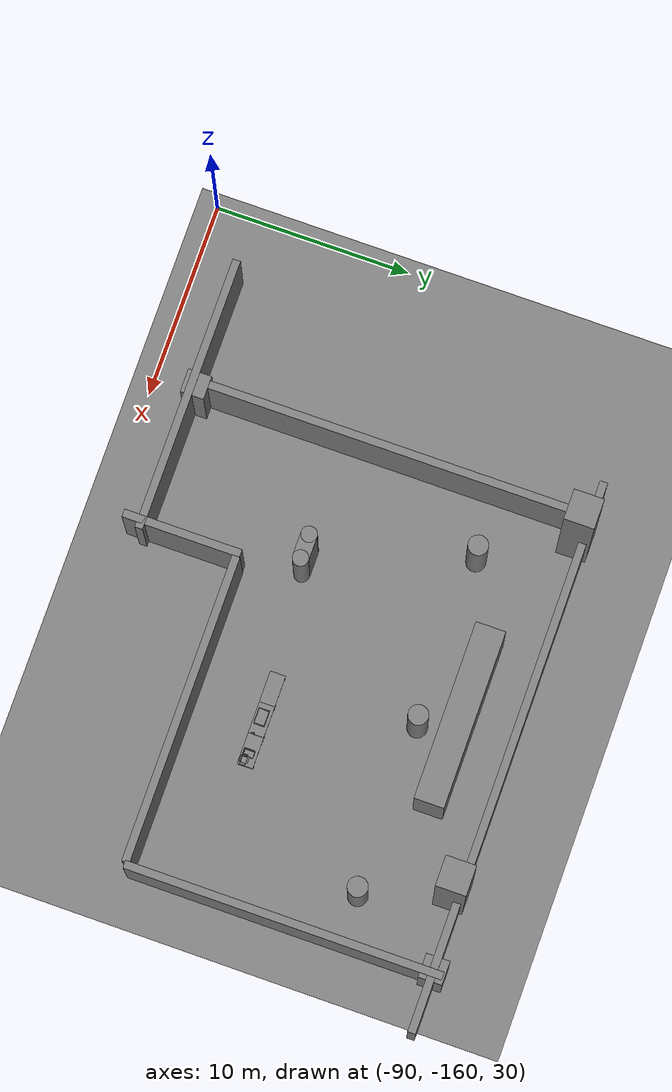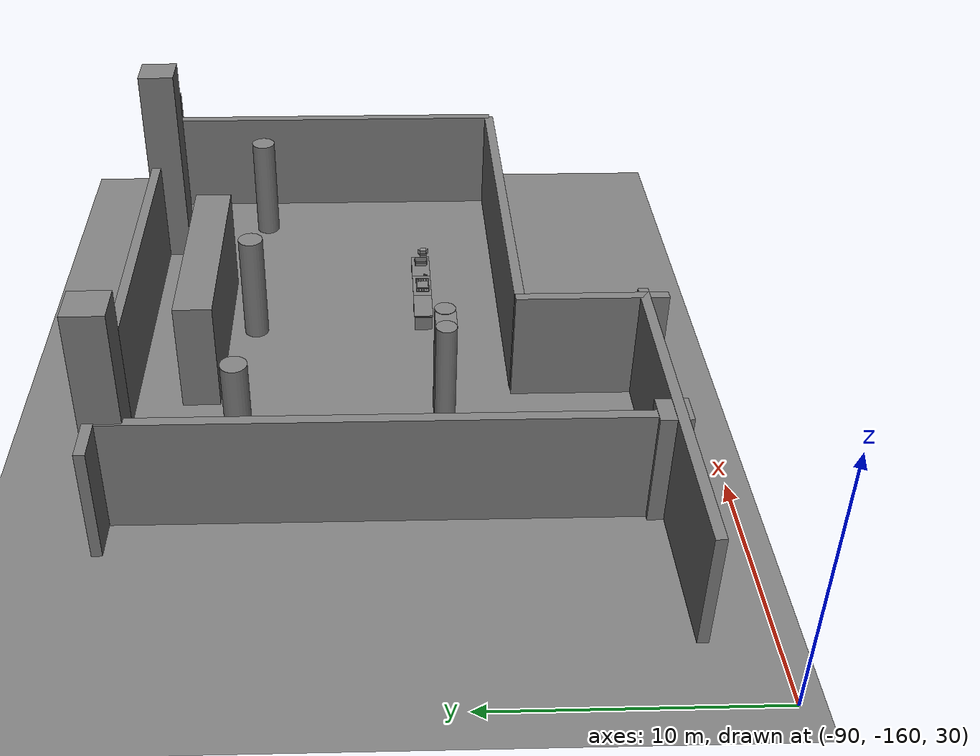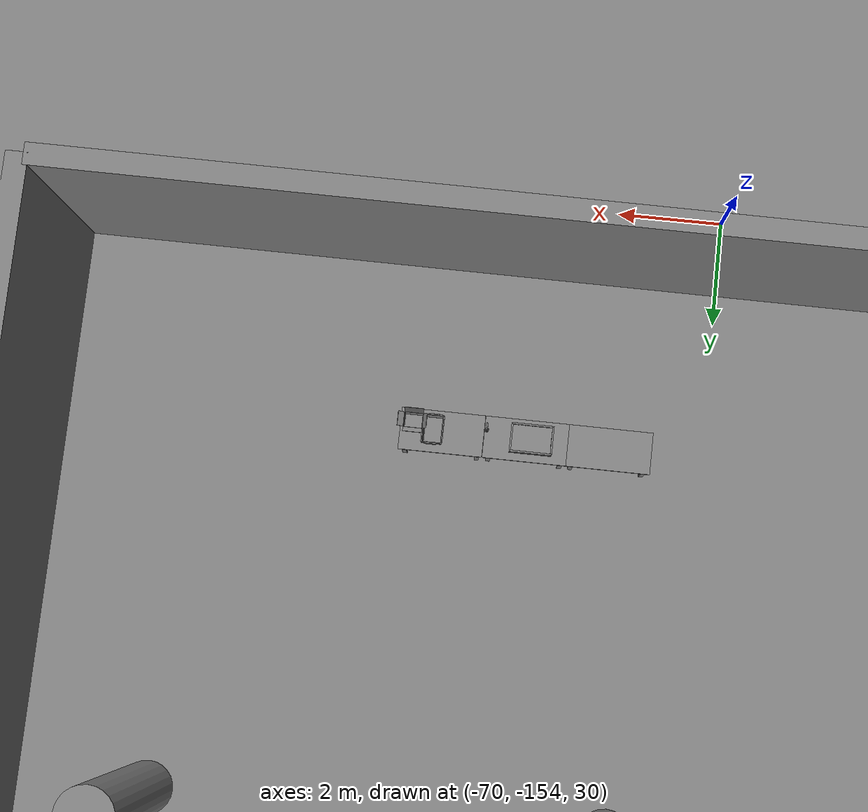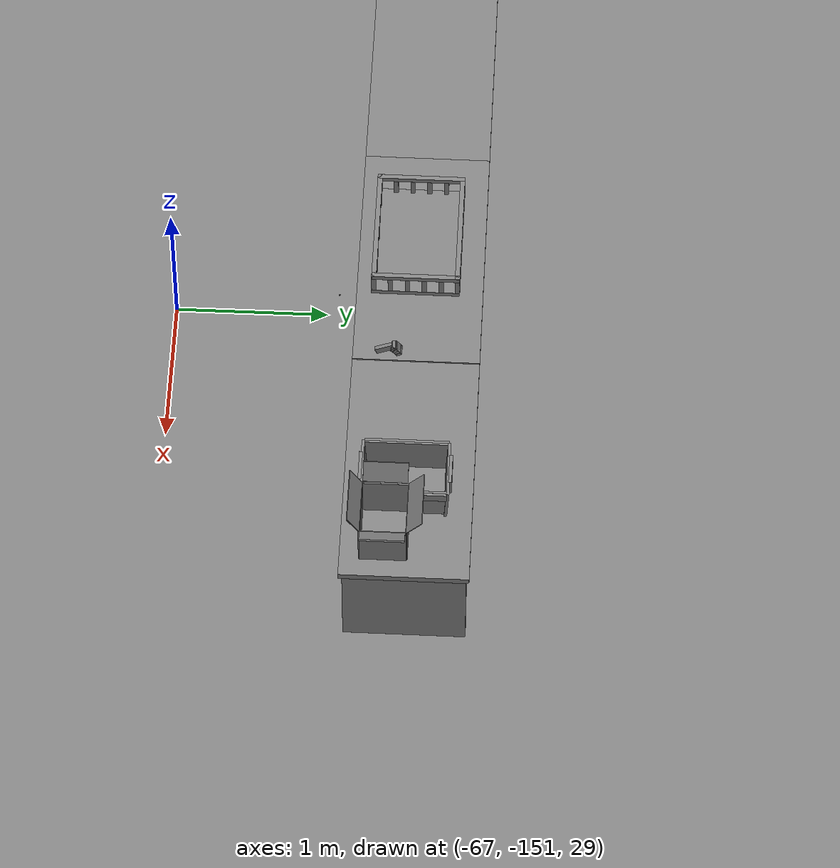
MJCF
<mujoco>
    <option gravity="0.000000000 0.000000000 -9.810000420" timestep="0.0049999999" integrator="implicitfast" density="1.225" viscosity="1.8000001e-05" noslip_iterations="10" iterations="100" sdf_iterations="50">
        <flag multiccd="disable"/>
    </option>
    <size memory="1000M"/>
    <compiler coordinate="local"/>
    <worldbody>
        <light cutoff="30" pos="0 1 1" dir="0 -1 -2"/>
        <light cutoff="30" pos="0 -1 1" dir="0 1 -2"/>
        <body pos="-64.866622925 -149.383972168 30.183746338" euler="89.999992371 89.999946594 0.000000000" name="openloong_gripper_2f85_fix_base_usda_bluebox_01">
            <geom contype="1" conaffinity="1" density="1000" type="box" material="" rgba="0.500000000 0.500000000 0.500000000 1.000000000" solimp="0.899999976 0.949999988 0.001000000" friction="1.000000000 0.005000000 0.000100000" solref="0.020000000 1.000000000" margin="0" condim="3" group="0" pos="0.276596069 0.187225342 0.000061035" quat="0.707107008 0.000077501 0.707106471 0.000077456" size="0.100000001 0.057999998 0.010000000" name="openloong_gripper_2f85_fix_base_usda_geom_4A1DB3C2_9324_4744_A07E_674E24B498D0"/>
            <geom contype="1" conaffinity="1" density="1000" type="box" material="" rgba="0.500000000 0.500000000 0.500000000 1.000000000" solimp="0.899999976 0.949999988 0.001000000" friction="1.000000000 0.005000000 0.000100000" solref="0.020000000 1.000000000" margin="0" condim="3" group="0" pos="0.000000000 0.002883911 0.000000000" quat="1.000000000 0.000000000 0.000000000 0.000000000" size="0.254000008 0.003000000 0.172000006" name="openloong_gripper_2f85_fix_base_usda_geom_1A5BF23C_63C7_42A7_AC86_2F01D6B1ED17"/>
            <geom contype="1" conaffinity="1" density="1000" type="box" material="" rgba="0.500000000 0.500000000 0.500000000 1.000000000" solimp="0.899999976 0.949999988 0.001000000" friction="1.000000000 0.005000000 0.000100000" solref="0.020000000 1.000000000" margin="0" condim="3" group="0" pos="0.000015259 0.124874115 0.173477173" quat="0.999796450 0.020176515 -0.000000015 0.000000030" size="0.259999990 0.119999997 0.007000000" name="openloong_gripper_2f85_fix_base_usda_geom_B438AA18_3EA6_4D3C_AA76_ACF946145DCD"/>
            <geom contype="1" conaffinity="1" density="1000" type="box" material="" rgba="0.500000000 0.500000000 0.500000000 1.000000000" solimp="0.899999976 0.949999988 0.001000000" friction="1.000000000 0.005000000 0.000100000" solref="0.020000000 1.000000000" margin="0" condim="3" group="0" pos="0.000015259 0.124874115 -0.173477173" quat="0.999796450 -0.020176545 -0.000000015 0.000000000" size="0.259999990 0.119999997 0.007000000" name="openloong_gripper_2f85_fix_base_usda_geom_E85CDCD0_B154_4938_9F60_B7C4EDC9225B"/>
            <geom contype="1" conaffinity="1" density="1000" type="box" material="" rgba="0.500000000 0.500000000 0.500000000 1.000000000" solimp="0.899999976 0.949999988 0.001000000" friction="1.000000000 0.005000000 0.000100000" solref="0.020000000 1.000000000" margin="0" condim="3" group="0" pos="0.000015259 0.214012146 0.188980103" quat="0.999913096 0.013176724 0.000000015 0.000000000" size="0.259999990 0.029999999 0.012500000" name="openloong_gripper_2f85_fix_base_usda_geom_75DCFE25_45F6_4ECE_8526_B19738D9DE42"/>
            <geom contype="1" conaffinity="1" density="1000" type="box" material="" rgba="0.500000000 0.500000000 0.500000000 1.000000000" solimp="0.899999976 0.949999988 0.001000000" friction="1.000000000 0.005000000 0.000100000" solref="0.020000000 1.000000000" margin="0" condim="3" group="0" pos="-0.258346558 0.125289917 0.001876831" quat="0.702796996 -0.020792052 0.710783184 0.020769238" size="0.189999998 0.119999997 0.009000000" name="openloong_gripper_2f85_fix_base_usda_geom_73A61076_9337_404B_A161_F438FD3FD798"/>
            <geom contype="1" conaffinity="1" density="1000" type="box" material="" rgba="0.500000000 0.500000000 0.500000000 1.000000000" solimp="0.899999976 0.949999988 0.001000000" friction="1.000000000 0.005000000 0.000100000" solref="0.020000000 1.000000000" margin="0" condim="3" group="0" pos="0.000015259 0.214012146 -0.188980103" quat="0.999913096 -0.013176769 0.000000030 0.000000015" size="0.259999990 0.029999999 0.012500000" name="openloong_gripper_2f85_fix_base_usda_geom_6DA75E8B_19DC_4772_B60B_416424CEF027"/>
            <geom contype="1" conaffinity="1" density="1000" type="box" material="" rgba="0.500000000 0.500000000 0.500000000 1.000000000" solimp="0.899999976 0.949999988 0.001000000" friction="1.000000000 0.005000000 0.000100000" solref="0.020000000 1.000000000" margin="0" condim="3" group="0" pos="-0.276596069 0.187225342 0.000061035" quat="0.707106650 0.000077441 0.707106709 0.000077456" size="0.100000001 0.057999998 0.010000000" name="openloong_gripper_2f85_fix_base_usda_geom_387B5348_0C74_4B98_97A2_6300D48E2F19"/>
            <geom contype="1" conaffinity="1" density="1000" type="box" material="" rgba="0.500000000 0.500000000 0.500000000 1.000000000" solimp="0.899999976 0.949999988 0.001000000" friction="1.000000000 0.005000000 0.000100000" solref="0.020000000 1.000000000" margin="0" condim="3" group="0" pos="0.258346558 0.125289917 0.001876831" quat="0.702851534 0.018856451 0.710823834 -0.019329429" size="0.189999998 0.119999997 0.009000000" name="openloong_gripper_2f85_fix_base_usda_geom_755EDCB2_9B4A_4C34_9BA1_51D30E1EF979"/>
            <freejoint name="openloong_gripper_2f85_fix_base_usda_bluebox_01_joint"/>
            <site size="0.005000000 0.005000000 0.005000000" rgba="0.500000000 0.500000000 0.500000000 1.000000000" pos="0.000000000 0.000000000 0.000000000" quat="0.999961913 0.008726534 0.000000000 0.000000000" group="0" type="sphere" name="openloong_gripper_2f85_fix_base_usda_bluebox_01site"/>
        </body>
        <body pos="-64.496299744 -149.491867065 30.235729218" euler="0.000000000 0.000000000 89.999946594" name="openloong_gripper_2f85_fix_base_usda_cardboardbox_01">
            <geom contype="1" conaffinity="1" density="1000" type="box" material="" rgba="0.500000000 0.500000000 0.500000000 1.000000000" solimp="0.899999976 0.949999988 0.001000000" friction="1.000000000 0.005000000 0.000100000" solref="0.020000000 1.000000000" margin="0" condim="3" group="0" pos="-0.003166199 -0.004086494 0.005052090" quat="1.000000000 0.000000000 0.000000000 0.000000000" size="0.142499998 0.177500010 0.005000000" name="openloong_gripper_2f85_fix_base_usda_geom_3D88EF7D_311B_44E2_A560_58C8A60FD7CE"/>
            <geom contype="1" conaffinity="1" density="1000" type="box" material="" rgba="0.500000000 0.500000000 0.500000000 1.000000000" solimp="0.899999976 0.949999988 0.001000000" friction="1.000000000 0.005000000 0.000100000" solref="0.020000000 1.000000000" margin="0" condim="3" group="0" pos="-0.003166199 0.170316696 0.150570869" quat="1.000000000 0.000000000 0.000000000 0.000000000" size="0.142499998 0.005000000 0.149999991" name="openloong_gripper_2f85_fix_base_usda_geom_A9CFB248_8198_46C7_BD03_CEDE87C1EF44"/>
            <geom contype="1" conaffinity="1" density="1000" type="box" material="" rgba="0.500000000 0.500000000 0.500000000 1.000000000" solimp="0.899999976 0.949999988 0.001000000" friction="1.000000000 0.005000000 0.000100000" solref="0.020000000 1.000000000" margin="0" condim="3" group="0" pos="-0.147399902 -0.005307198 0.150570869" quat="1.000000000 0.000000000 0.000000000 0.000000000" size="0.005000000 0.177500010 0.149999991" name="openloong_gripper_2f85_fix_base_usda_geom_B297D9F9_EC8A_41D6_BC89_31236EE259BE"/>
            <geom contype="1" conaffinity="1" density="1000" type="box" material="" rgba="0.500000000 0.500000000 0.500000000 1.000000000" solimp="0.899999976 0.949999988 0.001000000" friction="1.000000000 0.005000000 0.000100000" solref="0.020000000 1.000000000" margin="0" condim="3" group="0" pos="0.140275955 -0.005307198 0.150570869" quat="1.000000000 0.000000000 0.000000000 0.000000000" size="0.005000000 0.177500010 0.149999991" name="openloong_gripper_2f85_fix_base_usda_geom_739D352B_1A96_4B86_9F68_CBAADC8EF286"/>
            <geom contype="1" conaffinity="1" density="1000" type="box" material="" rgba="0.500000000 0.500000000 0.500000000 1.000000000" solimp="0.899999976 0.949999988 0.001000000" friction="1.000000000 0.005000000 0.000100000" solref="0.020000000 1.000000000" margin="0" condim="3" group="0" pos="-0.003166199 -0.181550980 0.150570869" quat="1.000000000 0.000000000 0.000000000 0.000000000" size="0.142499998 0.005000000 0.149999991" name="openloong_gripper_2f85_fix_base_usda_geom_B48F14DE_60AE_4085_B890_F6C12A0E3C6F"/>
            <freejoint name="openloong_gripper_2f85_fix_base_usda_cardboardbox_01_joint"/>
            <site size="0.005000000 0.005000000 0.005000000" rgba="0.500000000 0.500000000 0.500000000 1.000000000" pos="0.000000000 0.000000000 0.000000000" quat="0.999961913 0.008726535 0.000000000 0.000000000" group="0" type="sphere" name="openloong_gripper_2f85_fix_base_usda_site_D7E11865_520D_4600_B695_6D5B6418CA00"/>
            <body pos="0.139160156 -0.004048347 0.301930904" euler="-179.999954224 49.383502960 179.999954224" name="openloong_gripper_2f85_fix_base_usda_A1_006">
                <geom contype="1" conaffinity="1" density="1000" type="box" material="" rgba="0.500000000 0.500000000 0.500000000 1.000000000" solimp="0.899999976 0.949999988 0.001000000" friction="1.000000000 0.005000000 0.000100000" solref="0.020000000 1.000000000" margin="0" condim="3" group="0" pos="-0.071587563 0.000009537 0.001745224" quat="0.999999881 0.000000000 0.000000000 0.000000000" size="0.071249999 0.179999992 0.002500000" name="openloong_gripper_2f85_fix_base_usda_geom_26365C65_D5E6_4A8E_99A7_B4D089572702"/>
                <joint armature="0" stiffness="0.07" damping="0.0099999998" axis="0.000000 1.000000 0.000000" type="hinge" name="openloong_gripper_2f85_fix_base_usda_A1_006"/>
            </body>
            <body pos="-0.145902634 -0.004086494 0.301938057" euler="-180.000000000 -60.000011444 -180.000000000" name="openloong_gripper_2f85_fix_base_usda_A2_006">
                <geom contype="1" conaffinity="1" density="1000" type="box" material="" rgba="0.500000000 0.500000000 0.500000000 1.000000000" solimp="0.899999976 0.949999988 0.001000000" friction="1.000000000 0.005000000 0.000100000" solref="0.020000000 1.000000000" margin="0" condim="3" group="0" pos="0.071268082 0.000009537 0.002717972" quat="0.000002921 0.000000000 -0.000000030 0.999999881" size="0.071249999 0.179999992 0.002500000" name="openloong_gripper_2f85_fix_base_usda_geom_BE4240EC_C21E_4F1E_A7B8_672D75AC9EE0"/>
                <joint armature="0" stiffness="0.07" damping="0.0099999998" axis="0.000000 1.000000 0.000000" type="hinge" name="openloong_gripper_2f85_fix_base_usda_A2_006"/>
            </body>
            <body pos="-0.003385544 0.175991058 0.301930904" euler="-125.858116150 -0.000004561 0.000002331" name="openloong_gripper_2f85_fix_base_usda_B2_006">
                <geom contype="1" conaffinity="1" density="1000" type="box" material="" rgba="0.500000000 0.500000000 0.500000000 1.000000000" solimp="0.899999976 0.949999988 0.001000000" friction="1.000000000 0.005000000 0.000100000" solref="0.020000000 1.000000000" margin="0" condim="3" group="0" pos="0.000009537 -0.070939064 -0.002470016" quat="0.999614120 0.027776197 -0.000000015 0.000000030" size="0.137500003 0.064999998 0.005000000" name="openloong_gripper_2f85_fix_base_usda_geom_A5554DAD_966C_4029_A5C8_04491CADCF7D"/>
                <joint armature="0" stiffness="0.07" damping="0.0099999998" axis="1.000000 0.000000 0.000000" type="hinge" name="openloong_gripper_2f85_fix_base_usda_B2_006"/>
            </body>
            <body pos="-0.003385544 -0.184140205 0.301938057" euler="147.805557251 0.000000000 0.000000000" name="openloong_gripper_2f85_fix_base_usda_B1_006">
                <geom contype="1" conaffinity="1" density="1000" type="box" material="" rgba="0.500000000 0.500000000 0.500000000 1.000000000" solimp="0.899999976 0.949999988 0.001000000" friction="1.000000000 0.005000000 0.000100000" solref="0.020000000 1.000000000" margin="0" condim="3" group="0" pos="-0.000028610 0.070202351 -0.002703667" quat="0.999614179 -0.027776167 0.000000000 0.000000000" size="0.137500003 0.064999998 0.005000000" name="openloong_gripper_2f85_fix_base_usda_geom_680BD6DB_AEBD_4E61_A05F_A0EAA0CF15D4"/>
                <joint armature="0" stiffness="0.07" damping="0.0099999998" axis="1.000000 0.000000 0.000000" type="hinge" name="openloong_gripper_2f85_fix_base_usda_B1_006"/>
            </body>
        </body>
        <body pos="-65.882858276 -149.481979370 30.229999542" euler="-64.487716675 0.000000000 0.000000000" name="openloong_gripper_2f85_fix_base_usda_Barcode">
            <geom contype="1" conaffinity="1" density="1000" type="box" material="" rgba="0.500000000 0.500000000 0.500000000 1.000000000" solimp="0.899999976 0.949999988 0.001000000" friction="1.000000000 0.005000000 0.000100000" solref="0.020000000 1.000000000" margin="0" condim="3" group="0" pos="0.000000000 0.013038635 0.001419067" quat="0.000000000 0.000000000 0.000000000 1.000000119" size="0.034000002 0.010000000 0.017999999" name="openloong_gripper_2f85_fix_base_usda_geom_F5BC9511_651B_4333_A950_CA416B3E6901"/>
            <geom contype="1" conaffinity="1" density="1000" type="box" material="" rgba="0.500000000 0.500000000 0.500000000 1.000000000" solimp="0.899999976 0.949999988 0.001000000" friction="1.000000000 0.005000000 0.000100000" solref="0.020000000 1.000000000" margin="0" condim="3" group="0" pos="0.000000000 -0.035301208 -0.007095337" quat="0.000000000 0.000000000 -0.043619365 0.999048233" size="0.028999999 0.010000000 0.020000000" name="openloong_gripper_2f85_fix_base_usda_geom_A82DC819_D4BC_4AB1_8A56_05AA114A8108"/>
            <geom contype="1" conaffinity="1" density="1000" type="box" material="" rgba="0.500000000 0.500000000 0.500000000 1.000000000" solimp="0.899999976 0.949999988 0.001000000" friction="1.000000000 0.005000000 0.000100000" solref="0.020000000 1.000000000" margin="0" condim="3" group="0" pos="0.000000000 -0.043411255 -0.011749268" quat="0.922262907 0.386563420 0.000000000 0.000000000" size="0.026000001 0.010000000 0.020000000" name="openloong_gripper_2f85_fix_base_usda_geom_34B28A5A_1CBD_43F2_8FE1_9F1F1CD31417"/>
            <geom contype="1" conaffinity="1" density="1000" type="box" material="" rgba="0.500000000 0.500000000 0.500000000 1.000000000" solimp="0.899999976 0.949999988 0.001000000" friction="1.000000000 0.005000000 0.000100000" solref="0.020000000 1.000000000" margin="0" condim="3" group="0" pos="0.000000000 -0.016967773 -0.031860352" quat="0.000000000 0.000000000 0.000000000 1.000000119" size="0.008000000 0.010000000 0.013000000" name="openloong_gripper_2f85_fix_base_usda_geom_66536D88_6599_4042_9370_8F25ECF6F2BB"/>
            <geom contype="1" conaffinity="1" density="1000" type="box" material="" rgba="0.500000000 0.500000000 0.500000000 1.000000000" solimp="0.899999976 0.949999988 0.001000000" friction="1.000000000 0.005000000 0.000100000" solref="0.020000000 1.000000000" margin="0" condim="3" group="0" pos="0.000000000 -0.001869202 0.000312805" quat="0.953716993 0.300705761 0.000000000 0.000000000" size="0.032000002 0.010000000 0.018999999" name="openloong_gripper_2f85_fix_base_usda_geom_FCC07C5E_9900_4B4C_A941_5C8249784907"/>
            <geom contype="1" conaffinity="1" density="1000" type="box" material="" rgba="0.500000000 0.500000000 0.500000000 1.000000000" solimp="0.899999976 0.949999988 0.001000000" friction="1.000000000 0.005000000 0.000100000" solref="0.020000000 1.000000000" margin="0" condim="3" group="0" pos="0.000000000 -0.019531250 -0.003173828" quat="0.953716993 0.300705761 0.000000000 0.000000000" size="0.030999999 0.010000000 0.020000000" name="openloong_gripper_2f85_fix_base_usda_geom_F6C8BF1C_F900_454D_B115_B4CE50833642"/>
            <geom contype="1" conaffinity="1" density="1000" type="box" material="" rgba="0.500000000 0.500000000 0.500000000 1.000000000" solimp="0.899999976 0.949999988 0.001000000" friction="1.000000000 0.005000000 0.000100000" solref="0.020000000 1.000000000" margin="0" condim="3" group="0" pos="0.000000000 -0.035301208 -0.007095337" quat="0.953716993 0.300705761 0.000000000 0.000000000" size="0.028999999 0.010000000 0.020000000" name="openloong_gripper_2f85_fix_base_usda_geom_D35C0292_E674_424E_BD08_9AB4808FF02E"/>
            <geom contype="1" conaffinity="1" density="1000" type="box" material="" rgba="0.500000000 0.500000000 0.500000000 1.000000000" solimp="0.899999976 0.949999988 0.001000000" friction="1.000000000 0.005000000 0.000100000" solref="0.020000000 1.000000000" margin="0" condim="3" group="0" pos="0.000000000 -0.042617798 -0.071121216" quat="0.000000000 0.000000000 0.000000000 1.000000119" size="0.013000000 0.021000000 0.059999999" name="openloong_gripper_2f85_fix_base_usda_geom_06AF969F_686A_4449_86CE_A040BEBE2D8B"/>
            <freejoint name="openloong_gripper_2f85_fix_base_usda_Barcode_joint"/>
            <site size="0.005000000 0.005000000 0.005000000" rgba="0.500000000 0.500000000 0.500000000 1.000000000" pos="0.000000000 0.000000000 0.000000000" quat="1.000000000 0.000000000 0.000000000 0.000000000" group="0" type="sphere" name="openloong_gripper_2f85_fix_base_usda_Barcode_site"/>
        </body>
        <body pos="-66.745018005 -149.392349243 30.184000015" euler="0.000000000 0.000000000 89.999946594" name="[22331017776446]_Basket_01">
            <geom contype="1" conaffinity="1" density="1000" type="box" material="" rgba="0.500000000 0.500000000 0.500000000 1.000000000" solimp="0.899999976 0.949999988 0.001000000" friction="1.000000000 0.005000000 0.000100000" solref="0.020000000 1.000000000" margin="0" condim="3" group="0" pos="-0.052425385 0.389207840 0.089787483" quat="0.707107008 0.000000000 0.000000000 0.707106411" size="0.014249999 0.014249999 0.059999999" name="[22331017776446]_geom_FB59A9C5_DE60_42B4_BA6C_7DDAB276C2A8"/>
            <geom contype="1" conaffinity="1" density="1000" type="box" material="" rgba="0.500000000 0.500000000 0.500000000 1.000000000" solimp="0.899999976 0.949999988 0.001000000" friction="1.000000000 0.005000000 0.000100000" solref="0.020000000 1.000000000" margin="0" condim="3" group="0" pos="0.264015198 -0.133043289 0.089787483" quat="0.707107008 0.000000000 0.000000000 0.707106411" size="0.014249999 0.014249999 0.059999999" name="[22331017776446]_geom_F1F29333_25CA_45D1_94C1_18E43318EA42"/>
            <geom contype="1" conaffinity="1" density="1000" type="box" material="" rgba="0.500000000 0.500000000 0.500000000 1.000000000" solimp="0.899999976 0.949999988 0.001000000" friction="1.000000000 0.005000000 0.000100000" solref="0.020000000 1.000000000" margin="0" condim="3" group="0" pos="-0.264015198 -0.265548706 0.089793205" quat="0.707107008 0.000000000 0.000000000 0.707106411" size="0.014249999 0.014249999 0.059999999" name="[22331017776446]_geom_05BE01E7_2295_4F9E_B624_82BD198F9C11"/>
            <geom contype="1" conaffinity="1" density="1000" type="box" material="" rgba="0.500000000 0.500000000 0.500000000 1.000000000" solimp="0.899999976 0.949999988 0.001000000" friction="1.000000000 0.005000000 0.000100000" solref="0.020000000 1.000000000" margin="0" condim="3" group="0" pos="-0.160263062 -0.389322281 0.089793205" quat="0.707107008 0.000000000 0.000000000 0.707106411" size="0.014249999 0.014249999 0.059999999" name="[22331017776446]_geom_C7AA4798_3084_4176_8191_EC95E56FF34E"/>
            <geom contype="1" conaffinity="1" density="1000" type="box" material="" rgba="0.500000000 0.500000000 0.500000000 1.000000000" solimp="0.899999976 0.949999988 0.001000000" friction="1.000000000 0.005000000 0.000100000" solref="0.020000000 1.000000000" margin="0" condim="3" group="0" pos="0.162265778 -0.389322281 0.089787483" quat="0.707107008 0.000000000 0.000000000 0.707106411" size="0.014249999 0.014249999 0.059999999" name="[22331017776446]_geom_7E38893B_0DFB_4BEA_9712_315C9C38746C"/>
            <geom contype="1" conaffinity="1" density="1000" type="box" material="" rgba="0.500000000 0.500000000 0.500000000 1.000000000" solimp="0.899999976 0.949999988 0.001000000" friction="1.000000000 0.005000000 0.000100000" solref="0.020000000 1.000000000" margin="0" condim="3" group="0" pos="0.264015198 0.389207840 0.089787483" quat="0.707107008 0.000000000 0.000000000 0.707106411" size="0.014249999 0.014249999 0.059999999" name="[22331017776446]_geom_57F88326_F1F3_4DBD_B76F_BEA047F830A2"/>
            <geom contype="1" conaffinity="1" density="1000" type="box" material="" rgba="0.500000000 0.500000000 0.500000000 1.000000000" solimp="0.899999976 0.949999988 0.001000000" friction="1.000000000 0.005000000 0.000100000" solref="0.020000000 1.000000000" margin="0" condim="3" group="0" pos="-0.264015198 -0.133043289 0.089793205" quat="0.707107008 0.000000000 0.000000000 0.707106411" size="0.014249999 0.014249999 0.059999999" name="[22331017776446]_geom_11E180FD_A724_4EC5_9CBF_CEF700D58D62"/>
            <geom contype="1" conaffinity="1" density="1000" type="box" material="" rgba="0.500000000 0.500000000 0.500000000 1.000000000" solimp="0.899999976 0.949999988 0.001000000" friction="1.000000000 0.005000000 0.000100000" solref="0.020000000 1.000000000" margin="0" condim="3" group="0" pos="-0.264026642 0.269256592 0.089793205" quat="0.707107008 0.000000000 0.000000000 0.707106411" size="0.014249999 0.014249999 0.059999999" name="[22331017776446]_geom_E59E4927_57FB_43C3_BA8B_E26FAB3FB322"/>
            <geom contype="1" conaffinity="1" density="1000" type="box" material="" rgba="0.500000000 0.500000000 0.500000000 1.000000000" solimp="0.899999976 0.949999988 0.001000000" friction="1.000000000 0.005000000 0.000100000" solref="0.020000000 1.000000000" margin="0" condim="3" group="0" pos="0.054462433 0.389207840 0.089787483" quat="0.707107008 0.000000000 0.000000000 0.707106411" size="0.014249999 0.014249999 0.059999999" name="[22331017776446]_geom_66B8959E_D120_48A7_B2C2_10CEF6DA51E9"/>
            <geom contype="1" conaffinity="1" density="1000" type="box" material="" rgba="0.500000000 0.500000000 0.500000000 1.000000000" solimp="0.899999976 0.949999988 0.001000000" friction="1.000000000 0.005000000 0.000100000" solref="0.020000000 1.000000000" margin="0" condim="3" group="0" pos="0.054462433 -0.389322281 0.089787483" quat="0.707107008 0.000000000 0.000000000 0.707106411" size="0.014249999 0.014249999 0.059999999" name="[22331017776446]_geom_E227F1AB_AADF_49F3_B2AC_545EDB8B4A62"/>
            <geom contype="1" conaffinity="1" density="1000" type="box" material="" rgba="0.500000000 0.500000000 0.500000000 1.000000000" solimp="0.899999976 0.949999988 0.001000000" friction="1.000000000 0.005000000 0.000100000" solref="0.020000000 1.000000000" margin="0" condim="3" group="0" pos="0.264015198 0.269256592 0.089793205" quat="0.707107008 0.000000000 0.000000000 0.707106411" size="0.014249999 0.014249999 0.059999999" name="[22331017776446]_geom_25388E05_CDBE_4235_9786_52DB61A29AD4"/>
            <geom contype="1" conaffinity="1" density="1000" type="box" material="" rgba="0.500000000 0.500000000 0.500000000 1.000000000" solimp="0.899999976 0.949999988 0.001000000" friction="1.000000000 0.005000000 0.000100000" solref="0.020000000 1.000000000" margin="0" condim="3" group="0" pos="0.264015198 -0.389322281 0.089787483" quat="0.707107008 0.000000000 0.000000000 0.707106411" size="0.014249999 0.014249999 0.059999999" name="[22331017776446]_geom_EC756369_97D9_4AC6_9189_CB3F8BE066EA"/>
            <geom contype="1" conaffinity="1" density="1000" type="box" material="" rgba="0.500000000 0.500000000 0.500000000 1.000000000" solimp="0.899999976 0.949999988 0.001000000" friction="1.000000000 0.005000000 0.000100000" solref="0.020000000 1.000000000" margin="0" condim="3" group="0" pos="0.000000000 0.000000000 0.015998840" quat="0.707107008 0.000000000 0.000000000 0.707106411" size="0.403499991 0.279000014 0.015750000" name="[22331017776446]_geom_F0E41B3C_7E7B_4070_AD76_60EF7857E876"/>
            <geom contype="1" conaffinity="1" density="1000" type="box" material="" rgba="0.500000000 0.500000000 0.500000000 1.000000000" solimp="0.899999976 0.949999988 0.001000000" friction="1.000000000 0.005000000 0.000100000" solref="0.020000000 1.000000000" margin="0" condim="3" group="0" pos="0.000000000 -0.389476776 0.163619041" quat="0.707107008 0.000000000 0.000000000 0.707106411" size="0.015000000 0.277500004 0.015750000" name="[22331017776446]_geom_4AE1F845_2BD8_430D_89FC_B78A7EB9CC93"/>
            <geom contype="1" conaffinity="1" density="1000" type="box" material="" rgba="0.500000000 0.500000000 0.500000000 1.000000000" solimp="0.899999976 0.949999988 0.001000000" friction="1.000000000 0.005000000 0.000100000" solref="0.020000000 1.000000000" margin="0" condim="3" group="0" pos="0.162265778 0.389207840 0.089787483" quat="0.707107008 0.000000000 0.000000000 0.707106411" size="0.014249999 0.014249999 0.059999999" name="[22331017776446]_geom_23C445C5_0A8D_411D_9348_7382F6BFA6F9"/>
            <geom contype="1" conaffinity="1" density="1000" type="box" material="" rgba="0.500000000 0.500000000 0.500000000 1.000000000" solimp="0.899999976 0.949999988 0.001000000" friction="1.000000000 0.005000000 0.000100000" solref="0.020000000 1.000000000" margin="0" condim="3" group="0" pos="0.000000000 0.389471054 0.163619041" quat="0.707107008 0.000000000 0.000000000 0.707106411" size="0.015000000 0.277500004 0.015750000" name="[22331017776446]_geom_942E760F_06EE_420A_97FC_52E7A91BD297"/>
            <geom contype="1" conaffinity="1" density="1000" type="box" material="" rgba="0.500000000 0.500000000 0.500000000 1.000000000" solimp="0.899999976 0.949999988 0.001000000" friction="1.000000000 0.005000000 0.000100000" solref="0.020000000 1.000000000" margin="0" condim="3" group="0" pos="-0.263511658 0.000000000 0.163619041" quat="0.707107008 0.000000000 0.000000000 0.707106411" size="0.403499991 0.015000000 0.015750000" name="[22331017776446]_geom_D4CFCB28_C746_4299_8ADC_14CB41D40016"/>
            <geom contype="1" conaffinity="1" density="1000" type="box" material="" rgba="0.500000000 0.500000000 0.500000000 1.000000000" solimp="0.899999976 0.949999988 0.001000000" friction="1.000000000 0.005000000 0.000100000" solref="0.020000000 1.000000000" margin="0" condim="3" group="0" pos="-0.264015198 0.141334534 0.089793205" quat="0.707107008 0.000000000 0.000000000 0.707106411" size="0.014249999 0.014249999 0.059999999" name="[22331017776446]_geom_02BDD58F_1D12_4C1B_85F1_AC28FAAA8872"/>
            <geom contype="1" conaffinity="1" density="1000" type="box" material="" rgba="0.500000000 0.500000000 0.500000000 1.000000000" solimp="0.899999976 0.949999988 0.001000000" friction="1.000000000 0.005000000 0.000100000" solref="0.020000000 1.000000000" margin="0" condim="3" group="0" pos="0.264015198 -0.265548706 0.089787483" quat="0.707107008 0.000000000 0.000000000 0.707106411" size="0.014249999 0.014249999 0.059999999" name="[22331017776446]_geom_E25A96E3_4622_4B22_8668_7D085DA59846"/>
            <geom contype="1" conaffinity="1" density="1000" type="box" material="" rgba="0.500000000 0.500000000 0.500000000 1.000000000" solimp="0.899999976 0.949999988 0.001000000" friction="1.000000000 0.005000000 0.000100000" solref="0.020000000 1.000000000" margin="0" condim="3" group="0" pos="-0.160263062 0.389207840 0.089787483" quat="0.707107008 0.000000000 0.000000000 0.707106411" size="0.014249999 0.014249999 0.059999999" name="[22331017776446]_geom_BA57E14B_C895_4E6A_8D01_50B4C78E87F4"/>
            <geom contype="1" conaffinity="1" density="1000" type="box" material="" rgba="0.500000000 0.500000000 0.500000000 1.000000000" solimp="0.899999976 0.949999988 0.001000000" friction="1.000000000 0.005000000 0.000100000" solref="0.020000000 1.000000000" margin="0" condim="3" group="0" pos="-0.052425385 -0.389322281 0.089787483" quat="0.707107008 0.000000000 0.000000000 0.707106411" size="0.014249999 0.014249999 0.059999999" name="[22331017776446]_geom_7BBFB233_25BF_48AC_9DB6_93CA6E9D68BA"/>
            <geom contype="1" conaffinity="1" density="1000" type="box" material="" rgba="0.500000000 0.500000000 0.500000000 1.000000000" solimp="0.899999976 0.949999988 0.001000000" friction="1.000000000 0.005000000 0.000100000" solref="0.020000000 1.000000000" margin="0" condim="3" group="0" pos="-0.264026642 -0.389322281 0.089793205" quat="0.707107008 0.000000000 0.000000000 0.707106411" size="0.014249999 0.014249999 0.059999999" name="[22331017776446]_geom_075A066D_35ED_46BE_A799_338BFE559021"/>
            <geom contype="1" conaffinity="1" density="1000" type="box" material="" rgba="0.500000000 0.500000000 0.500000000 1.000000000" solimp="0.899999976 0.949999988 0.001000000" friction="1.000000000 0.005000000 0.000100000" solref="0.020000000 1.000000000" margin="0" condim="3" group="0" pos="0.264015198 0.141334534 0.089787483" quat="0.707107008 0.000000000 0.000000000 0.707106411" size="0.014249999 0.014249999 0.059999999" name="[22331017776446]_geom_2BE5C5C3_B0E3_43BD_B280_862FE373E89D"/>
            <geom contype="1" conaffinity="1" density="1000" type="box" material="" rgba="0.500000000 0.500000000 0.500000000 1.000000000" solimp="0.899999976 0.949999988 0.001000000" friction="1.000000000 0.005000000 0.000100000" solref="0.020000000 1.000000000" margin="0" condim="3" group="0" pos="-0.264015198 0.389207840 0.089793205" quat="0.707107008 0.000000000 0.000000000 0.707106411" size="0.014249999 0.014249999 0.059999999" name="[22331017776446]_geom_96EE25EC_26F7_47A5_A438_3E68CEB3B7F3"/>
            <geom contype="1" conaffinity="1" density="1000" type="box" material="" rgba="0.500000000 0.500000000 0.500000000 1.000000000" solimp="0.899999976 0.949999988 0.001000000" friction="1.000000000 0.005000000 0.000100000" solref="0.020000000 1.000000000" margin="0" condim="3" group="0" pos="0.264015198 0.004480362 0.089787483" quat="0.707107008 0.000000000 0.000000000 0.707106411" size="0.014249999 0.014249999 0.059999999" name="[22331017776446]_geom_144EE2C1_B8FA_48B0_A033_D5DEBC5F6206"/>
            <geom contype="1" conaffinity="1" density="1000" type="box" material="" rgba="0.500000000 0.500000000 0.500000000 1.000000000" solimp="0.899999976 0.949999988 0.001000000" friction="1.000000000 0.005000000 0.000100000" solref="0.020000000 1.000000000" margin="0" condim="3" group="0" pos="0.263694763 -0.000011444 0.163619041" quat="0.707107008 0.000000000 0.000000000 0.707106411" size="0.403499991 0.015000000 0.015750000" name="[22331017776446]_geom_8F7743EB_7A9B_4AA3_BFD8_33FB28FD0B3C"/>
            <geom contype="1" conaffinity="1" density="1000" type="box" material="" rgba="0.500000000 0.500000000 0.500000000 1.000000000" solimp="0.899999976 0.949999988 0.001000000" friction="1.000000000 0.005000000 0.000100000" solref="0.020000000 1.000000000" margin="0" condim="3" group="0" pos="-0.264015198 0.004480362 0.089793205" quat="0.707107008 0.000000000 0.000000000 0.707106411" size="0.014249999 0.014249999 0.059999999" name="[22331017776446]_geom_91DCA672_F48F_4DED_AF40_7920AD1AF76D"/>
            <freejoint name="[22331017776446]_joint_3EC6047F_4E6C_4E0E_B2B4_005AFAD36BE6"/>
        </body>
        <body pos="0.000000000 0.000000000 0.000000000" euler="0.000000000 0.000000000 0.000000000" name="Static Objects_Static Objects">
            <geom contype="1" conaffinity="1" density="1000" type="box" material="" rgba="0.500000000 0.500000000 0.500000000 1.000000000" solimp="0.899999976 0.949999988 0.001000000" friction="1.000000000 0.005000000 0.000100000" solref="0.020000000 1.000000000" margin="0" condim="3" group="0" pos="-67.544113159 -149.365814209 29.727830887" quat="0.500000417 0.499999970 0.499999553 0.499999970" size="0.381000012 0.319999993 0.041000001" name="Static Objects_geom_9B07A201_D304_4D84_AB37_57A070E02185"/>
            <geom contype="1" conaffinity="1" density="1000" type="box" material="" rgba="0.500000000 0.500000000 0.500000000 1.000000000" solimp="0.899999976 0.949999988 0.001000000" friction="1.000000000 0.005000000 0.000100000" solref="0.020000000 1.000000000" margin="0" condim="3" group="0" pos="-68.239501953 -149.365814209 30.086868286" quat="0.500000417 0.499999970 0.499999553 0.499999970" size="0.370999992 0.039500002 0.745000005" name="Static Objects_geom_4FBDEE11_66E4_4EF7_8ED6_E687887ECAA7"/>
            <geom contype="1" conaffinity="1" density="1000" type="box" material="" rgba="0.500000000 0.500000000 0.500000000 1.000000000" solimp="0.899999976 0.949999988 0.001000000" friction="1.000000000 0.005000000 0.000100000" solref="0.020000000 1.000000000" margin="0" condim="3" group="0" pos="-68.239501953 -149.365814209 30.147235870" quat="0.500000417 0.499999970 0.499999553 0.499999970" size="0.400000006 0.022000000 0.800000012" name="Static Objects_geom_048C05BF_97F6_4166_8C66_EA4953203082"/>
            <geom contype="1" conaffinity="1" density="1000" type="box" material="" rgba="0.500000000 0.500000000 0.500000000 1.000000000" solimp="0.899999976 0.949999988 0.001000000" friction="1.000000000 0.005000000 0.000100000" solref="0.020000000 1.000000000" margin="0" condim="3" group="0" pos="-68.934890747 -149.365814209 29.727830887" quat="0.500000417 0.499999970 0.499999553 0.499999970" size="0.381000012 0.319999993 0.041000001" name="Static Objects_geom_A73D8300_B5F2_4143_AF66_689001CC7C8E"/>
            <geom contype="1" conaffinity="1" density="1000" type="box" material="" rgba="0.500000000 0.500000000 0.500000000 1.000000000" solimp="0.899999976 0.949999988 0.001000000" friction="1.000000000 0.005000000 0.000100000" solref="0.020000000 1.000000000" margin="0" condim="3" group="0" pos="-68.239501953 -149.365814209 29.561563492" quat="0.500000417 0.499999970 0.499999553 0.499999970" size="0.020000000 0.022000000 0.660000026" name="Static Objects_geom_4B1168CF_D159_465E_B031_8A9A1D58770E"/>
            <geom contype="1" conaffinity="1" density="1000" type="box" material="" rgba="0.500000000 0.500000000 0.500000000 1.000000000" solimp="0.899999976 0.949999988 0.001000000" friction="1.000000000 0.005000000 0.000100000" solref="0.020000000 1.000000000" margin="0" condim="3" group="0" pos="-65.945671082 -149.365814209 29.727830887" quat="0.500000417 0.499999970 0.499999553 0.499999970" size="0.381000012 0.319999993 0.041000001" name="Static Objects_geom_9EC5900C_9523_49FC_B513_7DA9E917DD8A"/>
            <geom contype="1" conaffinity="1" density="1000" type="box" material="" rgba="0.500000000 0.500000000 0.500000000 1.000000000" solimp="0.899999976 0.949999988 0.001000000" friction="1.000000000 0.005000000 0.000100000" solref="0.020000000 1.000000000" margin="0" condim="3" group="0" pos="-66.641059875 -149.365814209 30.086868286" quat="0.500000417 0.499999970 0.499999553 0.499999970" size="0.370999992 0.039500002 0.745000005" name="Static Objects_geom_933E1B4B_2016_4275_BB21_D3FCE05E6766"/>
            <geom contype="1" conaffinity="1" density="1000" type="box" material="" rgba="0.500000000 0.500000000 0.500000000 1.000000000" solimp="0.899999976 0.949999988 0.001000000" friction="1.000000000 0.005000000 0.000100000" solref="0.020000000 1.000000000" margin="0" condim="3" group="0" pos="-66.641059875 -149.365814209 30.147235870" quat="0.500000417 0.499999970 0.499999553 0.499999970" size="0.400000006 0.022000000 0.800000012" name="Static Objects_geom_3EBB03F1_D0B3_49FE_9EAC_EE8EB6DC4C80"/>
            <geom contype="1" conaffinity="1" density="1000" type="box" material="" rgba="0.500000000 0.500000000 0.500000000 1.000000000" solimp="0.899999976 0.949999988 0.001000000" friction="1.000000000 0.005000000 0.000100000" solref="0.020000000 1.000000000" margin="0" condim="3" group="0" pos="-67.336448669 -149.365814209 29.727830887" quat="0.500000417 0.499999970 0.499999553 0.499999970" size="0.381000012 0.319999993 0.041000001" name="Static Objects_geom_69BB60E8_FD1B_486A_A503_D988C7DDC426"/>
            <geom contype="1" conaffinity="1" density="1000" type="box" material="" rgba="0.500000000 0.500000000 0.500000000 1.000000000" solimp="0.899999976 0.949999988 0.001000000" friction="1.000000000 0.005000000 0.000100000" solref="0.020000000 1.000000000" margin="0" condim="3" group="0" pos="-66.641059875 -149.365814209 29.561563492" quat="0.500000417 0.499999970 0.499999553 0.499999970" size="0.020000000 0.022000000 0.660000026" name="Static Objects_geom_A53A3AC5_A307_4C62_8F62_95BA2F4C2C07"/>
            <geom contype="1" conaffinity="1" density="1000" type="box" material="" rgba="0.500000000 0.500000000 0.500000000 1.000000000" solimp="0.899999976 0.949999988 0.001000000" friction="1.000000000 0.005000000 0.000100000" solref="0.020000000 1.000000000" margin="0" condim="3" group="0" pos="-64.338577271 -149.365814209 29.727830887" quat="0.500000417 0.499999970 0.499999553 0.499999970" size="0.381000012 0.319999993 0.041000001" name="Static Objects_geom_B1F5B1D4_AC0B_4BE8_A1DC_F02C59C7D60E"/>
            <geom contype="1" conaffinity="1" density="1000" type="box" material="" rgba="0.500000000 0.500000000 0.500000000 1.000000000" solimp="0.899999976 0.949999988 0.001000000" friction="1.000000000 0.005000000 0.000100000" solref="0.020000000 1.000000000" margin="0" condim="3" group="0" pos="-65.033966064 -149.365814209 30.086868286" quat="0.500000417 0.499999970 0.499999553 0.499999970" size="0.370999992 0.039500002 0.745000005" name="Static Objects_geom_2419C5A0_5039_4AD3_8022_29012CDC5551"/>
            <geom contype="1" conaffinity="1" density="1000" type="box" material="" rgba="0.500000000 0.500000000 0.500000000 1.000000000" solimp="0.899999976 0.949999988 0.001000000" friction="1.000000000 0.005000000 0.000100000" solref="0.020000000 1.000000000" margin="0" condim="3" group="0" pos="-65.033966064 -149.365814209 30.147235870" quat="0.500000417 0.499999970 0.499999553 0.499999970" size="0.400000006 0.022000000 0.800000012" name="Static Objects_geom_43A2E3EF_7DBF_426D_9749_07DD1FEF32FC"/>
            <geom contype="1" conaffinity="1" density="1000" type="box" material="" rgba="0.500000000 0.500000000 0.500000000 1.000000000" solimp="0.899999976 0.949999988 0.001000000" friction="1.000000000 0.005000000 0.000100000" solref="0.020000000 1.000000000" margin="0" condim="3" group="0" pos="-65.729354858 -149.365814209 29.727830887" quat="0.500000417 0.499999970 0.499999553 0.499999970" size="0.381000012 0.319999993 0.041000001" name="Static Objects_geom_DF303A89_44D0_46EC_9B51_021AB3DB91D3"/>
            <geom contype="1" conaffinity="1" density="1000" type="box" material="" rgba="0.500000000 0.500000000 0.500000000 1.000000000" solimp="0.899999976 0.949999988 0.001000000" friction="1.000000000 0.005000000 0.000100000" solref="0.020000000 1.000000000" margin="0" condim="3" group="0" pos="-65.033966064 -149.365814209 29.561563492" quat="0.500000417 0.499999970 0.499999553 0.499999970" size="0.020000000 0.022000000 0.660000026" name="Static Objects_geom_1330DAE9_DC6B_47B4_9DEA_01F6729E1C63"/>
            <geom contype="1" conaffinity="1" density="1000" type="box" material="" rgba="0.500000000 0.500000000 0.500000000 1.000000000" solimp="0.899999976 0.949999988 0.001000000" friction="1.000000000 0.005000000 0.000100000" solref="0.020000000 1.000000000" margin="0" condim="3" group="0" pos="-61.754566193 -137.853729248 33.906845093" quat="0.707107067 0.000000000 0.000000000 0.707106471" size="0.759999990 0.759999990 4.500000000" name="Static Objects_geom_5F280849_EFF9_4053_82D1_059F537CECFD"/>
            <geom contype="1" conaffinity="1" density="1000" type="box" material="" rgba="0.500000000 0.500000000 0.500000000 1.000000000" solimp="0.899999976 0.949999988 0.001000000" friction="1.000000000 0.005000000 0.000100000" solref="0.020000000 1.000000000" margin="0" condim="3" group="0" pos="-57.511135101 -144.927108765 31.707921982" quat="1.000000000 0.000000000 0.000000000 0.000000000" size="0.200000003 8.000000000 2.299999952" name="Static Objects_geom_44358769_6C34_4E3D_9F74_D232FF916EDF"/>
            <geom contype="1" conaffinity="1" density="1000" type="box" material="" rgba="0.500000000 0.500000000 0.500000000 1.000000000" solimp="0.899999976 0.949999988 0.001000000" friction="1.000000000 0.005000000 0.000100000" solref="0.020000000 1.000000000" margin="0" condim="3" group="0" pos="-80.517646790 -157.574050903 31.688196182" quat="0.707107067 0.000000000 0.000000000 0.707106471" size="0.600000024 0.600000024 2.299999952" name="Static Objects_geom_8E5A992A_C682_4455_A2C3_4C62D582E08B"/>
            <geom contype="1" conaffinity="1" density="1000" type="box" material="" rgba="0.500000000 0.500000000 0.500000000 1.000000000" solimp="0.899999976 0.949999988 0.001000000" friction="1.000000000 0.005000000 0.000100000" solref="0.020000000 1.000000000" margin="0" condim="3" group="0" pos="-80.711044312 -147.414932251 31.666158676" quat="1.000000000 0.000000000 0.000000000 0.000000000" size="0.200000003 10.000000000 2.299999952" name="Static Objects_geom_97694675_90C9_4D27_B697_4FB7C36DE90A"/>
            <geom contype="1" conaffinity="1" density="1000" type="box" material="" rgba="0.500000000 0.500000000 0.500000000 1.000000000" solimp="0.899999976 0.949999988 0.001000000" friction="1.000000000 0.005000000 0.000100000" solref="0.020000000 1.000000000" margin="0" condim="3" group="0" pos="-57.687217712 -137.434692383 31.688196182" quat="0.707107067 0.000000000 0.000000000 0.707106471" size="0.600000024 0.600000024 2.299999952" name="Static Objects_geom_A7096E69_1556_404F_81FF_E09CEA746E12"/>
            <geom contype="1" conaffinity="1" density="1000" type="box" material="" rgba="0.500000000 0.500000000 0.500000000 1.000000000" solimp="0.899999976 0.949999988 0.001000000" friction="1.000000000 0.005000000 0.000100000" solref="0.020000000 1.000000000" margin="0" condim="3" group="0" pos="-69.537033081 -140.263229370 31.714921951" quat="0.707107067 0.000000000 0.000000000 0.707106471" size="0.759999990 4.500000000 2.299999952" name="Static Objects_geom_AF32DF39_E972_4728_A679_829F90EA89A3"/>
            <geom contype="1" conaffinity="1" density="1000" type="box" material="" rgba="0.500000000 0.500000000 0.500000000 1.000000000" solimp="0.899999976 0.949999988 0.001000000" friction="1.000000000 0.005000000 0.000100000" solref="0.020000000 1.000000000" margin="0" condim="3" group="0" pos="-80.073638916 -137.853713989 33.906845093" quat="0.707107067 0.000000000 0.000000000 0.707106471" size="0.759999990 0.759999990 4.500000000" name="Static Objects_geom_822FE398_B7F4_4715_8012_23C86933BBD4"/>
            <geom contype="1" conaffinity="1" density="1000" type="box" material="" rgba="0.500000000 0.500000000 0.500000000 1.000000000" solimp="0.899999976 0.949999988 0.001000000" friction="1.000000000 0.005000000 0.000100000" solref="0.020000000 1.000000000" margin="0" condim="3" group="0" pos="-73.406707764 -155.734664917 31.707921982" quat="1.000000000 0.000000000 0.000000000 0.000000000" size="0.200000003 3.000000000 2.299999952" name="Static Objects_geom_3139A3AF_18D5_4A16_80EE_6D8082F11ED8"/>
            <geom contype="1" conaffinity="1" density="1000" type="box" material="" rgba="0.500000000 0.500000000 0.500000000 1.000000000" solimp="0.899999976 0.949999988 0.001000000" friction="1.000000000 0.005000000 0.000100000" solref="0.020000000 1.000000000" margin="0" condim="3" group="0" pos="-68.497543335 -137.448257446 31.707921982" quat="0.707107067 0.000000000 0.000000000 0.707106471" size="0.200000003 14.000000000 2.299999952" name="Static Objects_geom_B9C7AC57_3CF6_4238_9E04_E23D8281BAEE"/>
            <geom contype="1" conaffinity="1" density="1000" type="cylinder" material="" rgba="0.500000000 0.500000000 0.500000000 1.000000000" solimp="0.899999976 0.949999988 0.001000000" friction="1.000000000 0.005000000 0.000100000" solref="0.020000000 1.000000000" margin="0" condim="3" group="0" pos="-68.868522644 -142.134506226 31.711090088" quat="0.707107067 0.000000000 0.000000000 0.707106471" size="0.509999990 2.299999952 1.000000000" name="Static Objects_geom_9FF42FEE_2578_4687_97E9_690E4FD9F96D"/>
            <geom contype="1" conaffinity="1" density="1000" type="plane" material="" rgba="0.500000000 0.500000000 0.500000000 1.000000000" solimp="0.899999976 0.949999988 0.001000000" friction="1.000000000 0.005000000 0.000100000" solref="0.020000000 1.000000000" margin="0" condim="3" group="0" pos="-72.873703003 -147.131927490 29.409669876" quat="1.000000000 0.000000000 0.000000000 0.000000000" size="18.000000000 14.000000000 1.000000000" name="Static Objects_geom_96B9AC65_DA7C_4739_9207_91E68F7AF139"/>
            <geom contype="1" conaffinity="1" density="1000" type="box" material="" rgba="0.500000000 0.500000000 0.500000000 1.000000000" solimp="0.899999976 0.949999988 0.001000000" friction="1.000000000 0.005000000 0.000100000" solref="0.020000000 1.000000000" margin="0" condim="3" group="0" pos="-79.943580627 -157.782272339 31.707921982" quat="0.707107067 0.000000000 0.000000000 0.707106471" size="0.200000003 7.000000000 2.299999952" name="Static Objects_geom_FBC7B7A0_21E9_48B9_ADDF_385DAE670D2D"/>
            <geom contype="1" conaffinity="1" density="1000" type="box" material="" rgba="0.500000000 0.500000000 0.500000000 1.000000000" solimp="0.899999976 0.949999988 0.001000000" friction="1.000000000 0.005000000 0.000100000" solref="0.020000000 1.000000000" margin="0" condim="3" group="0" pos="-65.421028137 -152.903442383 31.707921982" quat="0.707107067 0.000000000 0.000000000 0.707106471" size="0.200000003 7.800000191 2.299999952" name="Static Objects_geom_5DC87AA4_223B_4586_8FF4_CF9673A400C0"/>
            <geom contype="1" conaffinity="1" density="1000" type="box" material="" rgba="0.500000000 0.500000000 0.500000000 1.000000000" solimp="0.899999976 0.949999988 0.001000000" friction="1.000000000 0.005000000 0.000100000" solref="0.020000000 1.000000000" margin="0" condim="3" group="0" pos="-74.776908875 -149.964416504 31.688196182" quat="1.000000000 0.000000000 0.000000000 0.000000000" size="0.600000024 0.409999996 2.299999952" name="Static Objects_geom_22767027_5949_45A5_A0FD_6F5302175F51"/>
            <geom contype="1" conaffinity="1" density="1000" type="cylinder" material="" rgba="0.500000000 0.500000000 0.500000000 1.000000000" solimp="0.899999976 0.949999988 0.001000000" friction="1.000000000 0.005000000 0.000100000" solref="0.020000000 1.000000000" margin="0" condim="3" group="0" pos="-60.161884308 -142.134506226 31.711090088" quat="0.707107067 0.000000000 0.000000000 0.707106471" size="0.509999990 2.299999952 1.000000000" name="Static Objects_geom_8E2DC807_CD67_4007_AF6F_63EEDBF86247"/>
            <geom contype="1" conaffinity="1" density="1000" type="cylinder" material="" rgba="0.500000000 0.500000000 0.500000000 1.000000000" solimp="0.899999976 0.949999988 0.001000000" friction="1.000000000 0.005000000 0.000100000" solref="0.020000000 1.000000000" margin="0" condim="3" group="0" pos="-75.382453918 -149.963455200 31.711090088" quat="0.707107067 0.000000000 0.000000000 0.707106471" size="0.409999996 2.299999952 1.000000000" name="Static Objects_geom_2599AC80_1FD1_4DCF_9A8C_C0005E6F0CD0"/>
            <geom contype="1" conaffinity="1" density="1000" type="cylinder" material="" rgba="0.500000000 0.500000000 0.500000000 1.000000000" solimp="0.899999976 0.949999988 0.001000000" friction="1.000000000 0.005000000 0.000100000" solref="0.020000000 1.000000000" margin="0" condim="3" group="0" pos="-74.154960632 -149.963455200 31.711090088" quat="0.707107067 0.000000000 0.000000000 0.707106471" size="0.409999996 2.299999952 1.000000000" name="Static Objects_geom_6B405AE6_8E2C_4B56_A87D_31C3F2070DFE"/>
            <geom contype="1" conaffinity="1" density="1000" type="cylinder" material="" rgba="0.500000000 0.500000000 0.500000000 1.000000000" solimp="0.899999976 0.949999988 0.001000000" friction="1.000000000 0.005000000 0.000100000" solref="0.020000000 1.000000000" margin="0" condim="3" group="0" pos="-77.566612244 -142.134506226 31.711090088" quat="0.707107067 0.000000000 0.000000000 0.707106471" size="0.509999990 2.299999952 1.000000000" name="Static Objects_geom_ACA5106B_7EA7_40F4_9EAC_5671AEEE4453"/>
        </body>
        <body pos="-66.291030884 -149.869689941 29.018842697" euler="0.000000000 0.000000000 89.999946594" mocap="true" name="openloong_gripper_2f85_fix_base_usda_leftHandMocap"/>
        <body pos="-66.291030884 -149.869689941 29.018842697" euler="0.000000000 0.000000000 89.999946594" mocap="true" name="openloong_gripper_2f85_fix_base_usda_rightHandMocap"/>
        <body pos="-66.291030884 -149.869689941 30.218843460" euler="0.000000000 0.000000000 89.999946594" name="openloong_gripper_2f85_fix_base_usda_base_link">
            <geom contype="1" conaffinity="1" density="1000" type="mesh" material="" rgba="0.783999979 0.783999979 0.783999979 1.000000000" solimp="0.899999976 0.949999988 0.001000000" friction="1.000000000 0.005000000 0.000100000" solref="0.020000000 1.000000000" margin="0" condim="3" group="3" mesh="base_link" pos="0.000000000 0.000000000 0.000000000" quat="1.000000000 0.000000000 0.000000000 0.000000000" size="1.000000000 1.000000000 1.000000000" name="openloong_gripper_2f85_fix_base_usda__geom_7_B55963C6_A211_4D3F_A436_A94113173383"/>
            <site size="0.005000000 0.005000000 0.005000000" rgba="0.500000000 0.500000000 0.500000000 1.000000000" pos="0.000000000 0.000000000 0.000000000" quat="1.000000000 0.000000000 0.000000000 0.000000000" group="0" type="sphere" name="openloong_gripper_2f85_fix_base_usda_imu"/>
            <inertial mass="22.447001" pos="-0.005664100 -0.001336700 0.238289997" diaginertia="0.374352545 0.277180195 0.220617250" quat="0.999247074 0.035235517 -0.015086859 0.006023135"/>
            <body pos="0.000000000 0.000000000 0.299997330" euler="0.000000000 0.000000000 0.000000000" name="openloong_gripper_2f85_fix_base_usda_dummy_body">
                <geom contype="1" conaffinity="1" density="1000" type="sphere" material="" rgba="0.783999979 0.783999979 0.783999979 1.000000000" solimp="0.899999976 0.949999988 0.001000000" friction="1.000000000 0.005000000 0.000100000" solref="0.020000000 1.000000000" margin="0" condim="3" group="3" pos="0.000000000 0.000000000 0.000000000" quat="1.000000000 0.000000000 0.000000000 0.000000000" size="0.010000000 0.000000000 0.000000000" name="openloong_gripper_2f85_fix_base_usda__geom_8_614C6781_3CEB_46E8_836F_C24BF06FBDD6"/>
                <joint armature="0.0099999998" stiffness="0" damping="0.1" axis="0.000000 0.000000 1.000000" type="hinge" name="openloong_gripper_2f85_fix_base_usda_dummy_joint"/>
                <site size="0.010000000 0.005000000 0.005000000" rgba="0.500000000 0.500000000 0.500000000 1.000000000" pos="0.000000000 0.000000000 0.000000000" quat="1.000000000 0.000000000 0.000000000 0.000000000" group="3" type="sphere" name="openloong_gripper_2f85_fix_base_usda_dummy_site"/>
            </body>
            <body pos="0.009002686 0.000000000 0.406400681" euler="0.000000000 0.000000000 0.000000000" name="openloong_gripper_2f85_fix_base_usda_Link_head_yaw">
                <geom contype="1" conaffinity="1" density="1000" type="mesh" material="" rgba="0.783999979 0.783999979 0.783999979 1.000000000" solimp="0.899999976 0.949999988 0.001000000" friction="1.000000000 0.005000000 0.000100000" solref="0.020000000 1.000000000" margin="0" condim="3" group="3" mesh="Link_head_yaw" pos="0.000000000 0.000000000 0.000000000" quat="1.000000000 0.000000000 0.000000000 0.000000000" size="1.000000000 1.000000000 1.000000000" name="openloong_gripper_2f85_fix_base_usda__geom_10_8F6F2D92_4178_42E7_B628_88D8EBCF1372"/>
                <inertial mass="0.84249002" pos="0.000000000 -0.002081400 0.044801001" diaginertia="0.000700588 0.000629000 0.000553812" quat="0.706933022 -0.015675601 0.015677100 0.706933022"/>
                <body pos="0.000000000 -0.034599304 0.048500061" euler="0.000000000 0.000000000 0.000000000" name="openloong_gripper_2f85_fix_base_usda_Link_head_pitch">
                    <geom contype="1" conaffinity="1" density="1000" type="mesh" material="" rgba="0.783999979 0.783999979 0.783999979 1.000000000" solimp="0.899999976 0.949999988 0.001000000" friction="1.000000000 0.005000000 0.000100000" solref="0.020000000 1.000000000" margin="0" condim="3" group="3" mesh="Link_head_pitch" pos="0.000000000 0.000000000 0.000000000" quat="1.000000000 0.000000000 0.000000000 0.000000000" size="1.000000000 1.000000000 1.000000000" name="openloong_gripper_2f85_fix_base_usda__geom_12_9AD46BE3_5DCD_4E62_8748_1B70EF040399"/>
                    <inertial mass="1.3943" pos="0.020569000 0.033004001 0.125000000" diaginertia="0.006381400 0.006289940 0.004481460" quat="0.973390222 0.008406822 0.228157058 0.019624906"/>
                    <body pos="0.000000000 0.029998779 0.000000000" euler="0.000000000 0.000000000 0.000000000" name="openloong_gripper_2f85_fix_base_usda_neck_center_body">
                        <site size="0.010000000 0.005000000 0.005000000" rgba="0.500000000 0.500000000 0.500000000 1.000000000" pos="0.000000000 0.000000000 0.000000000" quat="1.000000000 0.000000000 0.000000000 0.000000000" group="3" type="sphere" name="openloong_gripper_2f85_fix_base_usda_neck_center_site"/>
                        <body pos="0.020004272 0.000000000 0.149999619" euler="-0.000002229 39.998176575 -90.000205994" name="openloong_gripper_2f85_fix_base_usda_camera_head">
                            <site size="0.010000000 0.005000000 0.005000000" rgba="0.500000000 0.500000000 0.500000000 1.000000000" pos="0.000000000 0.000000000 0.000000000" quat="1.000000000 0.000000000 0.000000000 0.000000000" group="3" type="sphere" name="openloong_gripper_2f85_fix_base_usda_camera_head_site"/>
                        </body>
                    </body>
                </body>
            </body>
            <body pos="0.003997803 -0.161598206 0.392200470" euler="0.000000000 0.000000000 0.000000000" name="openloong_gripper_2f85_fix_base_usda_Link_arm_r_01">
                <geom contype="1" conaffinity="1" density="1000" type="mesh" material="" rgba="0.783999979 0.783999979 0.783999979 1.000000000" solimp="0.899999976 0.949999988 0.001000000" friction="1.000000000 0.005000000 0.000100000" solref="0.020000000 1.000000000" margin="0" condim="3" group="3" mesh="Link_arm_r_01" pos="0.000000000 0.000000000 0.000000000" quat="1.000000000 0.000000000 0.000000000 0.000000000" size="1.000000000 1.000000000 1.000000000" name="openloong_gripper_2f85_fix_base_usda__geom_14_6E15C353_64C7_468F_ABB9_0AE1182CD7CC"/>
                <joint armature="0.0099999998" stiffness="0" damping="1" axis="0.000000 -1.000000 0.000000" limited="true" range="-170.000015259 170.000015259" type="hinge" name="openloong_gripper_2f85_fix_base_usda_J_arm_r_01"/>
                <inertial mass="0.75641" pos="0.004494600 -0.038293999 -0.000001874" diaginertia="0.000842990 0.000803050 0.000587120" quat="-0.000163502 0.707098067 0.000812463 0.707115054"/>
                <body pos="-0.041992188 -0.041000366 0.000000000" euler="0.000000000 0.000000000 0.000000000" name="openloong_gripper_2f85_fix_base_usda_Link_arm_r_02">
                    <geom contype="1" conaffinity="1" density="1000" type="mesh" material="" rgba="0.783999979 0.783999979 0.783999979 1.000000000" solimp="0.899999976 0.949999988 0.001000000" friction="1.000000000 0.005000000 0.000100000" solref="0.020000000 1.000000000" margin="0" condim="3" group="3" mesh="Link_arm_r_02" pos="0.000000000 0.000000000 0.000000000" quat="1.000000000 0.000000000 0.000000000 0.000000000" size="1.000000000 1.000000000 1.000000000" name="openloong_gripper_2f85_fix_base_usda__geom_16_CB0DD502_FEB3_4A11_98E5_3324A8D39617"/>
                    <joint armature="0.0099999998" stiffness="0" damping="1" axis="-1.000000 0.000000 0.000000" limited="true" range="-105.000244141 105.000244141" type="hinge" name="openloong_gripper_2f85_fix_base_usda_J_arm_r_02"/>
                    <inertial mass="0.98500001" pos="0.041999999 -0.067430697 0.000000000" diaginertia="0.002262690 0.001730990 0.001154020" quat="0.500000000 0.500000000 -0.500000000 0.500000000"/>
                    <body pos="0.041992188 -0.122596741 0.000000000" euler="0.000000000 0.000000000 0.000000000" name="openloong_gripper_2f85_fix_base_usda_Link_arm_r_03">
                        <geom contype="1" conaffinity="1" density="1000" type="mesh" material="" rgba="0.783999979 0.783999979 0.783999979 1.000000000" solimp="0.899999976 0.949999988 0.001000000" friction="1.000000000 0.005000000 0.000100000" solref="0.020000000 1.000000000" margin="0" condim="3" group="3" mesh="Link_arm_r_03" pos="0.000000000 0.000000000 0.000000000" quat="1.000000000 0.000000000 0.000000000 0.000000000" size="1.000000000 1.000000000 1.000000000" name="openloong_gripper_2f85_fix_base_usda__geom_18_904BC08C_5949_4B95_B58D_E4599543D927"/>
                        <joint armature="0.0099999998" stiffness="0" damping="1" axis="0.000000 -1.000000 0.000000" limited="true" range="-170.000015259 170.000015259" type="hinge" name="openloong_gripper_2f85_fix_base_usda_J_arm_r_03"/>
                        <inertial mass="0.95899999" pos="-0.001413580 -0.164663002 0.020757901" diaginertia="0.002101340 0.002064590 0.000754802" quat="0.560480952 0.454391927 -0.443732947 0.531497955"/>
                        <body pos="0.035293579 -0.177406311 0.023998260" euler="0.000000000 0.000000000 0.000000000" name="openloong_gripper_2f85_fix_base_usda_Link_arm_r_04">
                            <geom contype="1" conaffinity="1" density="1000" type="mesh" material="" rgba="0.783999979 0.783999979 0.783999979 1.000000000" solimp="0.899999976 0.949999988 0.001000000" friction="1.000000000 0.005000000 0.000100000" solref="0.020000000 1.000000000" margin="0" condim="3" group="3" mesh="Link_arm_r_04" pos="0.000000000 0.000000000 0.000000000" quat="1.000000000 0.000000000 0.000000000 0.000000000" size="1.000000000 1.000000000 1.000000000" name="openloong_gripper_2f85_fix_base_usda__geom_20_AA4BC513_9F52_487C_B513_F9A9502442DE"/>
                            <joint armature="0.0099999998" stiffness="0" damping="1" axis="-1.000000 0.000000 0.000000" limited="true" range="0.000000000 170.000015259" type="hinge" name="openloong_gripper_2f85_fix_base_usda_J_arm_r_04"/>
                            <inertial mass="0.60000002" pos="-0.038727000 -0.060766999 -0.021003000" diaginertia="0.001092610 0.000712422 0.000645102" quat="0.327701002 0.632602990 -0.467366993 0.523443997"/>
                            <body pos="-0.035293579 -0.103492737 -0.023998260" euler="0.000000000 0.000000000 0.000000000" name="openloong_gripper_2f85_fix_base_usda_Link_arm_r_05">
                                <geom contype="1" conaffinity="1" density="1000" type="mesh" material="" rgba="0.783999979 0.783999979 0.783999979 1.000000000" solimp="0.899999976 0.949999988 0.001000000" friction="1.000000000 0.005000000 0.000100000" solref="0.020000000 1.000000000" margin="0" condim="3" group="3" mesh="Link_arm_r_05" pos="0.000000000 0.000000000 0.000000000" quat="1.000000000 0.000000000 0.000000000 0.000000000" size="1.000000000 1.000000000 1.000000000" name="openloong_gripper_2f85_fix_base_usda__geom_22_5FCDE472_E86A_4CFD_BAD0_307B2E6B8B03"/>
                                <joint armature="0.0099999998" stiffness="0" damping="1" axis="0.000000 -1.000000 0.000000" limited="true" range="-170.000015259 170.000015259" type="hinge" name="openloong_gripper_2f85_fix_base_usda_J_arm_r_05"/>
                                <inertial mass="0.68976003" pos="0.000032712 -0.068658002 -0.000111780" diaginertia="0.002522510 0.002411100 0.000448695" quat="0.707660973 0.706543028 -0.002603360 0.002470550"/>
                                <body pos="-0.026489258 -0.196502686 0.000000000" euler="0.000000000 0.000000000 0.000000000" name="openloong_gripper_2f85_fix_base_usda_Link_arm_r_06">
                                    <geom contype="1" conaffinity="1" density="1000" type="mesh" material="" rgba="0.783999979 0.783999979 0.783999979 1.000000000" solimp="0.899999976 0.949999988 0.001000000" friction="1.000000000 0.005000000 0.000100000" solref="0.020000000 1.000000000" margin="0" condim="3" group="3" mesh="Link_arm_r_06" pos="0.000000000 0.000000000 0.000000000" quat="1.000000000 0.000000000 0.000000000 0.000000000" size="1.000000000 1.000000000 1.000000000" name="openloong_gripper_2f85_fix_base_usda__geom_24_5D5D174D_4979_4E1B_8C71_7C8999085136"/>
                                    <joint armature="0.0099999998" stiffness="0" damping="1" axis="1.000000 0.000000 0.000000" limited="true" range="-105.000244141 105.000244141" type="hinge" name="openloong_gripper_2f85_fix_base_usda_J_arm_r_06"/>
                                    <inertial mass="0.28" pos="0.026078001 -0.000000896 0.001663700" diaginertia="0.000156930 0.000145601 0.000104979" quat="0.707080841 0.001851080 0.001883810 0.707127810"/>
                                    <body pos="0.026489258 0.000000000 0.031799316" euler="0.000000000 0.000000000 0.000000000" name="openloong_gripper_2f85_fix_base_usda_Link_arm_r_07">
                                        <geom contype="1" conaffinity="1" density="1000" type="mesh" material="" rgba="0.783999979 0.783999979 0.783999979 1.000000000" solimp="0.899999976 0.949999988 0.001000000" friction="1.000000000 0.005000000 0.000100000" solref="0.020000000 1.000000000" margin="0" condim="3" group="3" mesh="Link_arm_r_07" pos="0.000000000 0.000000000 0.000000000" quat="1.000000000 0.000000000 0.000000000 0.000000000" size="1.000000000 1.000000000 1.000000000" name="openloong_gripper_2f85_fix_base_usda__geom_26_FF787B7B_B13B_413E_95F9_D358226C9163"/>
                                        <joint armature="0.0099999998" stiffness="0" damping="1" axis="0.000000 0.000000 1.000000" limited="true" range="-60.000133514 60.000133514" type="hinge" name="openloong_gripper_2f85_fix_base_usda_J_arm_r_07"/>
                                        <inertial mass="0.61353999" pos="-0.007859000 -0.158170000 -0.027736001" diaginertia="0.003037610 0.002570910 0.000729379" quat="0.427542925 0.443532884 -0.553093910 0.560867906"/>
                                        <body pos="0.000000000 0.286994934 -0.270000458" euler="150.000350952 -0.000001649 -0.000000442" name="openloong_gripper_2f85_fix_base_usda_camera_wrist_r">
                                            <site size="0.010000000 0.005000000 0.005000000" rgba="0.500000000 0.500000000 0.500000000 1.000000000" pos="0.000000000 0.000000000 0.000000000" quat="1.000000000 0.000000000 0.000000000 0.000000000" group="3" type="sphere" name="openloong_gripper_2f85_fix_base_usda_camera_wrist_r_site"/>
                                        </body>
                                        <body pos="0.000000000 -0.220008850 -0.033002853" euler="0.000000000 0.000000000 179.999969482" name="openloong_gripper_2f85_fix_base_usda_ee_center_body_r">
                                            <site size="0.010000000 0.005000000 0.005000000" rgba="0.500000000 0.500000000 0.500000000 1.000000000" pos="0.000000000 0.000000000 0.000000000" quat="1.000000000 0.000000000 0.000000000 0.000000000" group="3" type="sphere" name="openloong_gripper_2f85_fix_base_usda_ee_center_site_r"/>
                                        </body>
                                        <body pos="0.000000000 -0.066001892 -0.031000137" euler="89.999984741 0.000000000 180.000000000" name="openloong_gripper_2f85_fix_base_usda_zbr_base_link">
                                            <geom contype="1" conaffinity="1" density="1000" type="mesh" material="" rgba="0.783999979 0.783999979 0.783999979 1.000000000" solimp="0.899999976 0.949999988 0.001000000" friction="1.000000000 0.005000000 0.000100000" solref="0.020000000 1.000000000" margin="0" condim="3" group="3" mesh="base" pos="0.000000000 0.000003815 -0.000007629" quat="1.000000000 0.000000000 0.000000000 0.000000000" size="1.000000238 1.000000238 1.000000238" name="openloong_gripper_2f85_fix_base_usda__geom_30_1BABE525_1706_4C0A_B683_43479BC92F35"/>
                                            <inertial mass="0.77744102" pos="0.000000000 -0.000027039 0.035467502" diaginertia="0.000260285 0.000225381 0.000152708" quat="0.999998808 -0.001528488 0.000000000 0.000000000"/>
                                            <body pos="-0.030609138 0.004745484 0.065696731" euler="-89.999984741 -0.000000000 0.000000000" name="openloong_gripper_2f85_fix_base_usda_r_left_driver">
                                                <geom contype="1" conaffinity="1" density="1000" type="mesh" material="" rgba="0.783999979 0.783999979 0.783999979 1.000000000" solimp="0.899999976 0.949999988 0.001000000" friction="1.000000000 0.005000000 0.000100000" solref="0.020000000 1.000000000" margin="0" condim="3" group="3" mesh="driver" pos="0.030609138 0.054901138 -0.004699708" quat="0.707106829 0.707106709 0.000000000 -0.000000000" size="1.000000238 1.000000238 1.000000238" name="openloong_gripper_2f85_fix_base_usda__geom_32_ABE61DFB_E1BB_4CAA_9FDA_6498C7B76637"/>
                                                <joint armature="0.0049999999" stiffness="0" damping="0.1" axis="0.000000 0.000000 1.000000" limited="true" range="0.000000000 51.566200256" type="hinge" name="openloong_gripper_2f85_fix_base_usda_r_left_driver_joint"/>
                                                <inertial mass="0.0089956298" pos="0.000000000 0.017754700 0.001073140" diaginertia="0.000001724 0.000001609 0.000000322" quat="0.681301236 0.732003212 0.000000000 0.000000000"/>
                                                <body pos="-0.031402595 0.004524232 -0.010200503" euler="0.000000000 0.000000000 180.000000000" name="openloong_gripper_2f85_fix_base_usda_r_left_coupler">
                                                    <geom contype="1" conaffinity="1" density="1000" type="mesh" material="" rgba="0.783999979 0.783999979 0.783999979 1.000000000" solimp="0.899999976 0.949999988 0.001000000" friction="1.000000000 0.005000000 0.000100000" solref="0.020000000 1.000000000" margin="0" condim="3" group="3" mesh="coupler" pos="-0.062011734 -0.050354015 0.005500795" quat="0.707106829 -0.707106709 0.000000000 -0.000000000" size="1.000000238 1.000000238 1.000000238" name="openloong_gripper_2f85_fix_base_usda__geom_34_47F7B711_11AD_4DA3_B780_35B80AE8D0F5"/>
                                                    <inertial mass="0.0140974" pos="0.000000000 0.003012090 0.023217499" diaginertia="0.000004162 0.000003522 0.000000888" quat="0.705635548 -0.045590367 0.045590367 0.705635548"/>
                                                </body>
                                            </body>
                                            <body pos="-0.012695315 -0.012001040 0.072212234" euler="-89.999984741 -0.000000000 0.000000000" name="openloong_gripper_2f85_fix_base_usda_r_left_spring_link">
                                                <geom contype="1" conaffinity="1" density="1000" type="mesh" material="" rgba="0.783999979 0.783999979 0.783999979 1.000000000" solimp="0.899999976 0.949999988 0.001000000" friction="1.000000000 0.005000000 0.000100000" solref="0.020000000 1.000000000" margin="0" condim="3" group="3" mesh="spring_link" pos="0.012695315 0.061416641 0.012050631" quat="0.707106829 0.707106709 0.000000000 -0.000000000" size="1.000000238 1.000000238 1.000000238" name="openloong_gripper_2f85_fix_base_usda__geom_36_5DE83DF9_0C8A_462D_AE5D_9505E762817A"/>
                                                <joint armature="0.001" stiffness="0.050000001" damping="0.00125" axis="0.000000 0.000000 1.000000" limited="true" range="-17.000000000 51.566200256" type="hinge" name="openloong_gripper_2f85_fix_base_usda_r_left_spring_link_joint"/>
                                                <inertial mass="0.0221642" pos="-0.000000009 0.018162400 0.021265799" diaginertia="0.000008969 0.000006717 0.000002639" quat="0.663403213 -0.244737089 0.244737089 0.663403213"/>
                                                <body pos="-0.038208015 -0.042503368 0.002950669" euler="180.000000000 0.000000000 -0.002185660" name="openloong_gripper_2f85_fix_base_usda_r_left_follower">
                                                    <geom contype="1" conaffinity="1" density="1000" type="mesh" material="" rgba="0.783999979 0.783999979 0.783999979 1.000000000" solimp="0.899999976 0.949999988 0.001000000" friction="1.000000000 0.005000000 0.000100000" solref="0.020000000 1.000000000" margin="0" condim="3" group="3" mesh="tongue" pos="0.050918590 -0.103920005 -0.009099962" quat="0.707106829 -0.707106709 0.000000030 0.000000030" size="1.000000238 1.000000238 1.000000238" name="openloong_gripper_2f85_fix_base_usda__geom_40_1D06B111_8305_434E_BFB3_42A2505BBD9E"/>
                                                    <geom contype="1" conaffinity="1" density="1000" type="mesh" material="" rgba="0.783999979 0.783999979 0.783999979 1.000000000" solimp="0.899999976 0.949999988 0.001000000" friction="1.000000000 0.005000000 0.000100000" solref="0.020000000 1.000000000" margin="0" condim="3" group="3" mesh="follower" pos="0.050918590 -0.103920005 -0.009099962" quat="0.707106829 -0.707106709 0.000000030 0.000000030" size="1.000000238 1.000000238 1.000000238" name="openloong_gripper_2f85_fix_base_usda__geom_39_212929D9_D12D_45CE_85C6_B71E289F5021"/>
                                                    <joint armature="0.001" stiffness="0" damping="0.1" axis="0.000000 0.000000 1.000000" limited="true" range="-49.999961853 51.566200256" type="hinge" name="openloong_gripper_2f85_fix_base_usda_r_left_follower"/>
                                                    <inertial mass="0.0125222" pos="0.000000000 -0.011046000 0.012478600" diaginertia="0.000002674 0.000002456 0.000000602" quat="0.986436546 0.164143041 0.000000000 0.000000000"/>
                                                    <body pos="-0.037765510 -0.103912376 -0.009099962" euler="-89.999984741 0.000000000 0.000004829" name="openloong_gripper_2f85_fix_base_usda_r_left_pad">
                                                        <geom contype="1" conaffinity="1" density="1000" type="box" material="" rgba="0.550000012 0.550000012 0.550000012 1.000000000" solimp="0.949999988 0.990000010 0.001000000" friction="0.699999988 0.005000000 0.000100000" solref="0.020000000 1.000000000" margin="0" condim="3" group="3" mass="1e-06" pos="0.043243419 0.000003815 0.119995147" quat="0.999999881 0.000000000 0.000000000 0.000000000" size="0.002000001 0.011000003 0.009375002" name="openloong_gripper_2f85_fix_base_usda_r_left_pad1_9B987A3E_01F9_46A5_8290_D0D4F38AC7B4"/>
                                                        <geom contype="1" conaffinity="1" density="1000" type="box" material="" rgba="0.449999988 0.449999988 0.449999988 1.000000000" solimp="0.949999988 0.990000010 0.001000000" friction="0.600000024 0.005000000 0.000100000" solref="0.020000000 1.000000000" margin="0" condim="3" group="3" mass="1e-06" pos="0.043243419 0.000003815 0.138748199" quat="0.999999881 0.000000000 0.000000000 0.000000000" size="0.002000001 0.011000003 0.009375002" name="openloong_gripper_2f85_fix_base_usda_r_left_pad2_CDE9E42B_9BB7_43D0_AA9D_E30A0B13885B"/>
                                                    </body>
                                                </body>
                                            </body>
                                            <body pos="0.030593880 -0.004753114 0.065696731" euler="89.999984741 0.000000000 180.000000000" name="openloong_gripper_2f85_fix_base_usda_r_right_driver">
                                                <geom contype="1" conaffinity="1" density="1000" type="mesh" material="" rgba="0.783999979 0.783999979 0.783999979 1.000000000" solimp="0.899999976 0.949999988 0.001000000" friction="1.000000000 0.005000000 0.000100000" solref="0.020000000 1.000000000" margin="0" condim="3" group="3" mesh="driver" pos="0.030593880 0.054901138 -0.004699708" quat="0.707106829 0.707106709 0.000000000 0.000000000" size="1.000000238 1.000000238 1.000000238" name="openloong_gripper_2f85_fix_base_usda__geom_42_A7961E12_08AC_43BE_B641_49F25FCEBE27"/>
                                                <joint armature="0.0049999999" stiffness="0" damping="0.1" axis="0.000000 0.000000 1.000000" limited="true" range="0.000000000 51.566200256" type="hinge" name="openloong_gripper_2f85_fix_base_usda_r_right_driver_joint"/>
                                                <inertial mass="0.0089956298" pos="0.000000000 0.017754700 0.001073140" diaginertia="0.000001724 0.000001609 0.000000322" quat="0.681301236 0.732003212 0.000000000 0.000000000"/>
                                                <body pos="-0.031417854 0.004531861 -0.010202411" euler="0.000000000 0.000000000 180.000000000" name="openloong_gripper_2f85_fix_base_usda_r_right_coupler">
                                                    <geom contype="1" conaffinity="1" density="1000" type="mesh" material="" rgba="0.783999979 0.783999979 0.783999979 1.000000000" solimp="0.899999976 0.949999988 0.001000000" friction="1.000000000 0.005000000 0.000100000" solref="0.020000000 1.000000000" margin="0" condim="3" group="3" mesh="coupler" pos="-0.062042251 -0.050376903 0.005500795" quat="0.707106829 -0.707106709 0.000000000 0.000000000" size="1.000000238 1.000000238 1.000000238" name="openloong_gripper_2f85_fix_base_usda__geom_44_13A9F2C6_CCCF_4473_BE22_471B8695F5DA"/>
                                                    <inertial mass="0.0140974" pos="0.000000000 0.003012090 0.023217499" diaginertia="0.000004162 0.000003522 0.000000888" quat="0.705635548 -0.045590367 0.045590367 0.705635548"/>
                                                </body>
                                            </body>
                                            <body pos="0.012695315 0.011997226 0.072219864" euler="89.999984741 0.000000000 180.000000000" name="openloong_gripper_2f85_fix_base_usda_r_right_spring_link">
                                                <geom contype="1" conaffinity="1" density="1000" type="mesh" material="" rgba="0.783999979 0.783999979 0.783999979 1.000000000" solimp="0.899999976 0.949999988 0.001000000" friction="1.000000000 0.005000000 0.000100000" solref="0.020000000 1.000000000" margin="0" condim="3" group="3" mesh="spring_link" pos="0.012695315 0.061424270 0.012048724" quat="0.707106829 0.707106709 0.000000000 0.000000000" size="1.000000238 1.000000238 1.000000238" name="openloong_gripper_2f85_fix_base_usda__geom_46_EE053806_0FEA_420E_9D53_C6451C43F07B"/>
                                                <joint armature="0.001" stiffness="0.050000001" damping="0.00125" axis="0.000000 0.000000 1.000000" limited="true" range="-17.000000000 51.566200256" type="hinge" name="openloong_gripper_2f85_fix_base_usda_r_right_spring_link_joint"/>
                                                <inertial mass="0.0221642" pos="-0.000000009 0.018162400 0.021265799" diaginertia="0.000008969 0.000006717 0.000002639" quat="0.663403213 -0.244737089 0.244737089 0.663403213"/>
                                                <body pos="-0.038208015 -0.042495739 0.002950669" euler="180.000000000 0.000000000 0.000000000" name="openloong_gripper_2f85_fix_base_usda_r_right_follower">
                                                    <geom contype="1" conaffinity="1" density="1000" type="mesh" material="" rgba="0.783999979 0.783999979 0.783999979 1.000000000" solimp="0.899999976 0.949999988 0.001000000" friction="1.000000000 0.005000000 0.000100000" solref="0.020000000 1.000000000" margin="0" condim="3" group="3" mesh="follower" pos="0.050888073 -0.103927635 -0.009099962" quat="0.707106829 -0.707106709 0.000000000 0.000000000" size="1.000000238 1.000000238 1.000000238" name="openloong_gripper_2f85_fix_base_usda__geom_50_74A187C4_1060_4239_AD1E_D10170CBF045"/>
                                                    <geom contype="1" conaffinity="1" density="1000" type="mesh" material="" rgba="0.783999979 0.783999979 0.783999979 1.000000000" solimp="0.899999976 0.949999988 0.001000000" friction="1.000000000 0.005000000 0.000100000" solref="0.020000000 1.000000000" margin="0" condim="3" group="3" mesh="tongue" pos="0.050888073 -0.103927635 -0.009099962" quat="0.707106829 -0.707106709 0.000000000 0.000000000" size="1.000000238 1.000000238 1.000000238" name="openloong_gripper_2f85_fix_base_usda__geom_49_C8AABC04_33D7_4090_B88C_38614B5F6A87"/>
                                                    <joint armature="0.001" stiffness="0" damping="0.1" axis="0.000000 0.000000 1.000000" limited="true" range="-49.999961853 51.566200256" type="hinge" name="openloong_gripper_2f85_fix_base_usda_r_right_follower_joint"/>
                                                    <inertial mass="0.0125222" pos="0.000000000 -0.011046000 0.012478600" diaginertia="0.000002674 0.000002456 0.000000602" quat="0.986436546 0.164143041 0.000000000 0.000000000"/>
                                                    <body pos="-0.037811287 -0.103927635 -0.009099962" euler="-89.999984741 0.000000000 0.000000000" name="openloong_gripper_2f85_fix_base_usda_r_right_pad">
                                                        <geom contype="1" conaffinity="1" density="1000" type="box" material="" rgba="0.449999988 0.449999988 0.449999988 1.000000000" solimp="0.949999988 0.990000010 0.001000000" friction="0.600000024 0.005000000 0.000100000" solref="0.020000000 1.000000000" margin="0" condim="3" group="3" mass="1e-06" pos="0.043258678 0.000000000 0.138748199" quat="1.000000000 0.000000000 0.000000000 0.000000000" size="0.002000001 0.011000003 0.009375002" name="openloong_gripper_2f85_fix_base_usda_r_right_pad2_E41FB767_E726_43FE_8123_AD11C42B6D5B"/>
                                                        <geom contype="1" conaffinity="1" density="1000" type="box" material="" rgba="0.550000012 0.550000012 0.550000012 1.000000000" solimp="0.949999988 0.990000010 0.001000000" friction="0.699999988 0.005000000 0.000100000" solref="0.020000000 1.000000000" margin="0" condim="3" group="3" mass="1e-06" pos="0.043258678 0.000003815 0.120002776" quat="1.000000000 0.000000000 0.000000000 0.000000000" size="0.002000001 0.011000003 0.009375002" name="openloong_gripper_2f85_fix_base_usda_r_right_pad1_F51381D8_1C73_4218_A340_EB35D84D98C5"/>
                                                    </body>
                                                </body>
                                            </body>
                                        </body>
                                    </body>
                                </body>
                            </body>
                        </body>
                    </body>
                </body>
            </body>
            <body pos="0.003997803 0.161590576 0.392200470" euler="0.000000000 0.000000000 0.000000000" name="openloong_gripper_2f85_fix_base_usda_Link_arm_l_01">
                <geom contype="1" conaffinity="1" density="1000" type="mesh" material="" rgba="0.783999979 0.783999979 0.783999979 1.000000000" solimp="0.899999976 0.949999988 0.001000000" friction="1.000000000 0.005000000 0.000100000" solref="0.020000000 1.000000000" margin="0" condim="3" group="3" mesh="Link_arm_l_01" pos="0.000000000 0.000000000 0.000000000" quat="1.000000000 0.000000000 0.000000000 0.000000000" size="1.000000000 1.000000000 1.000000000" name="openloong_gripper_2f85_fix_base_usda__geom_52_7A0EC480_42D9_45A4_9EB9_CBE9278D6BED"/>
                <joint armature="0.0099999998" stiffness="0" damping="1" axis="0.000000 1.000000 0.000000" limited="true" range="-170.000015259 170.000015259" type="hinge" name="openloong_gripper_2f85_fix_base_usda_J_arm_l_01"/>
                <inertial mass="0.75640601" pos="-0.004494650 0.038294200 -0.000001874" diaginertia="0.000842986 0.000803053 0.000587115" quat="-0.000812496 0.707115054 0.000163424 0.707098067"/>
                <body pos="0.042007446 0.041000366 0.000000000" euler="0.000000000 0.000000000 0.000000000" name="openloong_gripper_2f85_fix_base_usda_Link_arm_l_02">
                    <geom contype="1" conaffinity="1" density="1000" type="mesh" material="" rgba="0.783999979 0.783999979 0.783999979 1.000000000" solimp="0.899999976 0.949999988 0.001000000" friction="1.000000000 0.005000000 0.000100000" solref="0.020000000 1.000000000" margin="0" condim="3" group="3" mesh="Link_arm_l_02" pos="0.000000000 0.000000000 0.000000000" quat="1.000000000 0.000000000 0.000000000 0.000000000" size="1.000000000 1.000000000 1.000000000" name="openloong_gripper_2f85_fix_base_usda__geom_54_5B1C343A_E357_4ABE_959F_6563F6AC8B2B"/>
                    <joint armature="0.0099999998" stiffness="0" damping="1" axis="-1.000000 0.000000 0.000000" limited="true" range="-105.000244141 105.000244141" type="hinge" name="openloong_gripper_2f85_fix_base_usda_J_arm_l_02"/>
                    <inertial mass="0.98500001" pos="-0.041999999 0.067430697 0.000000000" diaginertia="0.002262690 0.001730990 0.001154020" quat="0.500000000 0.500000000 -0.500000000 0.500000000"/>
                    <body pos="-0.042007446 0.122596741 0.000000000" euler="0.000000000 0.000000000 0.000000000" name="openloong_gripper_2f85_fix_base_usda_Link_arm_l_03">
                        <geom contype="1" conaffinity="1" density="1000" type="mesh" material="" rgba="0.783999979 0.783999979 0.783999979 1.000000000" solimp="0.899999976 0.949999988 0.001000000" friction="1.000000000 0.005000000 0.000100000" solref="0.020000000 1.000000000" margin="0" condim="3" group="3" mesh="Link_arm_l_03" pos="0.000000000 0.000000000 0.000000000" quat="1.000000000 0.000000000 0.000000000 0.000000000" size="1.000000000 1.000000000 1.000000000" name="openloong_gripper_2f85_fix_base_usda__geom_56_D10F025E_9395_4913_95DD_CF187FD8FE09"/>
                        <joint armature="0.0099999998" stiffness="0" damping="1" axis="0.000000 1.000000 0.000000" limited="true" range="-170.000015259 170.000015259" type="hinge" name="openloong_gripper_2f85_fix_base_usda_J_arm_l_03"/>
                        <inertial mass="0.95899999" pos="0.001413580 0.164663002 0.020757901" diaginertia="0.002101340 0.002064590 0.000754802" quat="0.443732947 0.531497955 -0.560480952 0.454391927"/>
                        <body pos="-0.035293579 0.177406311 0.023998260" euler="0.000000000 0.000000000 0.000000000" name="openloong_gripper_2f85_fix_base_usda_Link_arm_l_04">
                            <geom contype="1" conaffinity="1" density="1000" type="mesh" material="" rgba="0.783999979 0.783999979 0.783999979 1.000000000" solimp="0.899999976 0.949999988 0.001000000" friction="1.000000000 0.005000000 0.000100000" solref="0.020000000 1.000000000" margin="0" condim="3" group="3" mesh="Link_arm_l_04" pos="0.000000000 0.000000000 0.000000000" quat="1.000000000 0.000000000 0.000000000 0.000000000" size="1.000000000 1.000000000 1.000000000" name="openloong_gripper_2f85_fix_base_usda__geom_58_F8C4F68B_D15A_41E1_A33E_1477901CC07E"/>
                            <joint armature="0.0099999998" stiffness="0" damping="1" axis="1.000000 0.000000 0.000000" limited="true" range="0.000000000 170.000015259" type="hinge" name="openloong_gripper_2f85_fix_base_usda_J_arm_l_04"/>
                            <inertial mass="0.60000002" pos="0.038727000 0.060767200 -0.021003200" diaginertia="0.001092570 0.000712419 0.000645098" quat="0.467370987 0.523440003 -0.327692002 0.632607996"/>
                            <body pos="0.035293579 0.103500366 -0.023998260" euler="0.000000000 0.000000000 0.000000000" name="openloong_gripper_2f85_fix_base_usda_Link_arm_l_05">
                                <geom contype="1" conaffinity="1" density="1000" type="mesh" material="" rgba="0.783999979 0.783999979 0.783999979 1.000000000" solimp="0.899999976 0.949999988 0.001000000" friction="1.000000000 0.005000000 0.000100000" solref="0.020000000 1.000000000" margin="0" condim="3" group="3" mesh="Link_arm_l_05" pos="0.000000000 0.000000000 0.000000000" quat="1.000000000 0.000000000 0.000000000 0.000000000" size="1.000000000 1.000000000 1.000000000" name="openloong_gripper_2f85_fix_base_usda__geom_60_234C4635_66EB_4E2E_83E0_DAF742D6D85E"/>
                                <joint armature="0.0099999998" stiffness="0" damping="1" axis="0.000000 1.000000 0.000000" limited="true" range="-170.000015259 170.000015259" type="hinge" name="openloong_gripper_2f85_fix_base_usda_J_arm_l_05"/>
                                <inertial mass="0.68976003" pos="-0.000032712 0.068658002 -0.000111780" diaginertia="0.002522510 0.002411100 0.000448695" quat="0.706543028 0.707660973 0.002470550 -0.002603360"/>
                                <body pos="0.026504517 0.196495056 0.000000000" euler="0.000000000 0.000000000 0.000000000" name="openloong_gripper_2f85_fix_base_usda_Link_arm_l_06">
                                    <geom contype="1" conaffinity="1" density="1000" type="mesh" material="" rgba="0.783999979 0.783999979 0.783999979 1.000000000" solimp="0.899999976 0.949999988 0.001000000" friction="1.000000000 0.005000000 0.000100000" solref="0.020000000 1.000000000" margin="0" condim="3" group="3" mesh="Link_arm_l_06" pos="0.000000000 0.000000000 0.000000000" quat="1.000000000 0.000000000 0.000000000 0.000000000" size="1.000000000 1.000000000 1.000000000" name="openloong_gripper_2f85_fix_base_usda__geom_62_CE162DD8_1077_4306_857E_935A1E37174E"/>
                                    <joint armature="0.0099999998" stiffness="0" damping="1" axis="-1.000000 0.000000 0.000000" limited="true" range="-105.000244141 105.000244141" type="hinge" name="openloong_gripper_2f85_fix_base_usda_J_arm_l_06"/>
                                    <inertial mass="0.28" pos="-0.026077701 0.000000896 0.001663730" diaginertia="0.000156927 0.000145598 0.000104981" quat="0.707080841 -0.001851280 -0.001884020 0.707127810"/>
                                    <body pos="-0.026504517 0.000000000 0.031799316" euler="0.000000000 0.000000000 0.000000000" name="openloong_gripper_2f85_fix_base_usda_Link_arm_l_07">
                                        <geom contype="1" conaffinity="1" density="1000" type="mesh" material="" rgba="0.783999979 0.783999979 0.783999979 1.000000000" solimp="0.899999976 0.949999988 0.001000000" friction="1.000000000 0.005000000 0.000100000" solref="0.020000000 1.000000000" margin="0" condim="3" group="3" mesh="Link_arm_l_07" pos="0.000000000 0.000000000 0.000000000" quat="1.000000000 0.000000000 0.000000000 0.000000000" size="1.000000000 1.000000000 1.000000000" name="openloong_gripper_2f85_fix_base_usda__geom_64_3AAE7869_0D89_496C_B7C6_A9B256FC218A"/>
                                        <joint armature="0.0099999998" stiffness="0" damping="1" axis="0.000000 0.000000 1.000000" limited="true" range="-60.000133514 60.000133514" type="hinge" name="openloong_gripper_2f85_fix_base_usda_J_arm_l_07"/>
                                        <inertial mass="0.61353999" pos="-0.007787200 0.157049999 -0.027733000" diaginertia="0.003037200 0.002570420 0.000729374" quat="0.443562120 0.427539080 -0.560871124 0.553070128"/>
                                        <body pos="0.000000000 -0.286994934 -0.270000458" euler="-150.000350952 0.000001955 179.976669312" name="openloong_gripper_2f85_fix_base_usda_camera_wrist_l">
                                            <site size="0.010000000 0.005000000 0.005000000" rgba="0.500000000 0.500000000 0.500000000 1.000000000" pos="0.000000000 0.000000000 0.000000000" quat="1.000000000 0.000000000 0.000000000 0.000000000" group="3" type="sphere" name="openloong_gripper_2f85_fix_base_usda_camera_wrist_l_site"/>
                                        </body>
                                        <body pos="0.000000000 0.220008850 -0.033002853" euler="0.000000000 0.000000000 0.000000000" name="openloong_gripper_2f85_fix_base_usda_ee_center_body">
                                            <site size="0.010000000 0.005000000 0.005000000" rgba="0.500000000 0.500000000 0.500000000 1.000000000" pos="0.000000000 0.000000000 0.000000000" quat="1.000000000 0.000000000 0.000000000 0.000000000" group="3" type="sphere" name="openloong_gripper_2f85_fix_base_usda_ee_center_site"/>
                                        </body>
                                        <body pos="0.000000000 0.066009521 -0.031000137" euler="-90.000007629 0.000000000 0.000000000" name="openloong_gripper_2f85_fix_base_usda_zbll_base_link">
                                            <geom contype="1" conaffinity="1" density="1000" type="mesh" material="" rgba="0.783999979 0.783999979 0.783999979 1.000000000" solimp="0.899999976 0.949999988 0.001000000" friction="1.000000000 0.005000000 0.000100000" solref="0.020000000 1.000000000" margin="0" condim="3" group="3" mesh="base" pos="0.000000000 0.000000000 0.000000000" quat="1.000000000 0.000000000 0.000000000 0.000000000" size="1.000000000 1.000000000 1.000000000" name="openloong_gripper_2f85_fix_base_usda__geom_68_6CBB5CE9_C069_400D_8137_EFA6CB33720B"/>
                                            <inertial mass="0.77744102" pos="0.000000000 -0.000027039 0.035467502" diaginertia="0.000260285 0.000225381 0.000152708" quat="0.999998808 -0.001528488 0.000000000 0.000000000"/>
                                            <body pos="-0.030578613 0.004755020 0.065696716" euler="-89.999984741 0.000000000 0.000000000" name="openloong_gripper_2f85_fix_base_usda_l_left_driver">
                                                <geom contype="1" conaffinity="1" density="1000" type="mesh" material="" rgba="0.783999979 0.783999979 0.783999979 1.000000000" solimp="0.899999976 0.949999988 0.001000000" friction="1.000000000 0.005000000 0.000100000" solref="0.020000000 1.000000000" margin="0" condim="3" group="3" mesh="driver" pos="0.030609131 0.054901123 -0.004699707" quat="0.707106829 0.707106709 0.000000000 0.000000000" size="1.000000000 1.000000000 1.000000000" name="openloong_gripper_2f85_fix_base_usda__geom_70_8C5DAFB1_51CD_4FD1_8926_3036A7D4B7EB"/>
                                                <joint armature="0.0049999999" stiffness="0" damping="0.1" axis="0.000000 0.000000 1.000000" limited="true" range="0.000000000 51.566200256" type="hinge" name="openloong_gripper_2f85_fix_base_usda_l_left_driver_joint"/>
                                                <inertial mass="0.0089956298" pos="0.000000000 0.017754700 0.001073140" diaginertia="0.000001724 0.000001609 0.000000322" quat="0.681301236 0.732003212 0.000000000 0.000000000"/>
                                                <body pos="-0.031402588 0.004531860 -0.010200500" euler="0.000000000 0.000000000 180.000000000" name="openloong_gripper_2f85_fix_base_usda_l_left_coupler">
                                                    <geom contype="1" conaffinity="1" density="1000" type="mesh" material="" rgba="0.783999979 0.783999979 0.783999979 1.000000000" solimp="0.899999976 0.949999988 0.001000000" friction="1.000000000 0.005000000 0.000100000" solref="0.020000000 1.000000000" margin="0" condim="3" group="3" mesh="coupler" pos="-0.062042236 -0.050369263 0.005500793" quat="0.707106829 -0.707106709 0.000000000 0.000000000" size="1.000000000 1.000000000 1.000000000" name="openloong_gripper_2f85_fix_base_usda__geom_72_BCF85683_9258_49CE_BA82_9E060BD6EF2A"/>
                                                    <inertial mass="0.0140974" pos="0.000000000 0.003012090 0.023217499" diaginertia="0.000004162 0.000003522 0.000000888" quat="0.705635548 -0.045590367 0.045590367 0.705635548"/>
                                                </body>
                                            </body>
                                            <body pos="-0.012680054 -0.011987686 0.072204590" euler="-89.999984741 0.000000000 0.000000000" name="openloong_gripper_2f85_fix_base_usda_l_left_spring_link">
                                                <geom contype="1" conaffinity="1" density="1000" type="mesh" material="" rgba="0.783999979 0.783999979 0.783999979 1.000000000" solimp="0.899999976 0.949999988 0.001000000" friction="1.000000000 0.005000000 0.000100000" solref="0.020000000 1.000000000" margin="0" condim="3" group="3" mesh="spring_link" pos="0.012725830 0.061431885 0.012050629" quat="0.707106829 0.707106709 0.000000000 0.000000000" size="1.000000000 1.000000000 1.000000000" name="openloong_gripper_2f85_fix_base_usda__geom_74_91E6E8A9_7EEA_4221_9260_45FB41E034C2"/>
                                                <joint armature="0.001" stiffness="0.050000001" damping="0.00125" axis="0.000000 0.000000 1.000000" limited="true" range="-17.000000000 51.566200256" type="hinge" name="openloong_gripper_2f85_fix_base_usda_l_left_spring_link_joint"/>
                                                <inertial mass="0.0221642" pos="-0.000000009 0.018162400 0.021265799" diaginertia="0.000008969 0.000006717 0.000002639" quat="0.663403213 -0.244737089 0.244737089 0.663403213"/>
                                                <body pos="-0.038192749 -0.042495728 0.002950668" euler="180.000000000 0.000000000 -0.002185660" name="openloong_gripper_2f85_fix_base_usda_l_left_follower">
                                                    <geom contype="1" conaffinity="1" density="1000" type="mesh" material="" rgba="0.783999979 0.783999979 0.783999979 1.000000000" solimp="0.899999976 0.949999988 0.001000000" friction="1.000000000 0.005000000 0.000100000" solref="0.020000000 1.000000000" margin="0" condim="3" group="3" mesh="follower" pos="0.050933838 -0.103919983 -0.009098053" quat="0.707106829 -0.707106650 0.000000000 -0.000000030" size="1.000000000 1.000000000 1.000000000" name="openloong_gripper_2f85_fix_base_usda__geom_77_D2F59500_B67E_4359_A3C8_C8DEFABBEB66"/>
                                                    <geom contype="1" conaffinity="1" density="1000" type="mesh" material="" rgba="0.783999979 0.783999979 0.783999979 1.000000000" solimp="0.899999976 0.949999988 0.001000000" friction="1.000000000 0.005000000 0.000100000" solref="0.020000000 1.000000000" margin="0" condim="3" group="3" mesh="tongue" pos="0.050933838 -0.103919983 -0.009098053" quat="0.707106829 -0.707106650 0.000000000 -0.000000030" size="1.000000000 1.000000000 1.000000000" name="openloong_gripper_2f85_fix_base_usda__geom_78_C1D851B7_42CC_4EA5_9DBA_D60234384D9B"/>
                                                    <joint armature="0.001" stiffness="0" damping="0.1" axis="0.000000 0.000000 1.000000" limited="true" range="-49.999961853 51.566200256" type="hinge" name="openloong_gripper_2f85_fix_base_usda_l_left_follower"/>
                                                    <inertial mass="0.0125222" pos="0.000000000 -0.011046000 0.012478600" diaginertia="0.000002674 0.000002456 0.000000602" quat="0.986436546 0.164143041 0.000000000 0.000000000"/>
                                                    <body pos="-0.037780762 -0.103919983 -0.009098053" euler="-89.999977112 0.000002415 -0.000002415" name="openloong_gripper_2f85_fix_base_usda_l_left_pad">
                                                        <geom contype="1" conaffinity="1" density="1000" type="box" material="" rgba="0.550000012 0.550000012 0.550000012 1.000000000" solimp="0.949999988 0.990000010 0.001000000" friction="0.699999988 0.005000000 0.000100000" solref="0.020000000 1.000000000" margin="0" condim="3" group="3" mass="1e-06" pos="0.043273926 0.000009537 0.119995117" quat="0.999999881 0.000000000 0.000000000 0.000000000" size="0.002000000 0.011000000 0.009375000" name="openloong_gripper_2f85_fix_base_usda_l_left_pad1_431D513B_32C0_41F4_9FE4_2F242EF7F719"/>
                                                        <geom contype="1" conaffinity="1" density="1000" type="box" material="" rgba="0.449999988 0.449999988 0.449999988 1.000000000" solimp="0.949999988 0.990000010 0.001000000" friction="0.600000024 0.005000000 0.000100000" solref="0.020000000 1.000000000" margin="0" condim="3" group="3" mass="1e-06" pos="0.043273926 0.000017166 0.138732910" quat="0.999999881 0.000000000 0.000000000 0.000000000" size="0.002000000 0.011000000 0.009375000" name="openloong_gripper_2f85_fix_base_usda_l_left_pad2_8AF1757F_5F9C_4A57_9556_01D55CAEAAA2"/>
                                                    </body>
                                                </body>
                                            </body>
                                            <body pos="0.030609131 -0.004739761 0.065689087" euler="89.999984741 0.000000000 180.000000000" name="openloong_gripper_2f85_fix_base_usda_l_right_driver">
                                                <geom contype="1" conaffinity="1" density="1000" type="mesh" material="" rgba="0.783999979 0.783999979 0.783999979 1.000000000" solimp="0.899999976 0.949999988 0.001000000" friction="1.000000000 0.005000000 0.000100000" solref="0.020000000 1.000000000" margin="0" condim="3" group="3" mesh="driver" pos="0.030593872 0.054901123 -0.004697800" quat="0.707106829 0.707106709 0.000000000 0.000000000" size="1.000000000 1.000000000 1.000000000" name="openloong_gripper_2f85_fix_base_usda__geom_80_2DBF8482_CAC1_4E7F_8D7E_F61240A15B98"/>
                                                <joint armature="0.0049999999" stiffness="0" damping="0.1" axis="0.000000 0.000000 1.000000" limited="true" range="0.000000000 51.566200256" type="hinge" name="openloong_gripper_2f85_fix_base_usda_l_right_driver_joint"/>
                                                <inertial mass="0.0089956298" pos="0.000000000 0.017754700 0.001073140" diaginertia="0.000001724 0.000001609 0.000000322" quat="0.681301236 0.732003212 0.000000000 0.000000000"/>
                                                <body pos="-0.031433105 0.004531860 -0.010198593" euler="0.000000000 0.000000000 180.000000000" name="openloong_gripper_2f85_fix_base_usda_l_right_coupler">
                                                    <geom contype="1" conaffinity="1" density="1000" type="mesh" material="" rgba="0.783999979 0.783999979 0.783999979 1.000000000" solimp="0.899999976 0.949999988 0.001000000" friction="1.000000000 0.005000000 0.000100000" solref="0.020000000 1.000000000" margin="0" condim="3" group="3" mesh="coupler" pos="-0.062011719 -0.050369263 0.005502701" quat="0.707106829 -0.707106709 0.000000000 0.000000000" size="1.000000000 1.000000000 1.000000000" name="openloong_gripper_2f85_fix_base_usda__geom_82_A3A9853A_E1F2_4D76_BF8C_9439993357ED"/>
                                                    <inertial mass="0.0140974" pos="0.000000000 0.003012090 0.023217499" diaginertia="0.000004162 0.000003522 0.000000888" quat="0.705635548 -0.045590367 0.045590367 0.705635548"/>
                                                </body>
                                            </body>
                                            <body pos="0.012710571 0.012010574 0.072204590" euler="89.999984741 0.000000000 180.000000000" name="openloong_gripper_2f85_fix_base_usda_l_right_spring_link">
                                                <geom contype="1" conaffinity="1" density="1000" type="mesh" material="" rgba="0.783999979 0.783999979 0.783999979 1.000000000" solimp="0.899999976 0.949999988 0.001000000" friction="1.000000000 0.005000000 0.000100000" solref="0.020000000 1.000000000" margin="0" condim="3" group="3" mesh="spring_link" pos="0.012695312 0.061416626 0.012052536" quat="0.707106829 0.707106709 0.000000000 0.000000000" size="1.000000000 1.000000000 1.000000000" name="openloong_gripper_2f85_fix_base_usda__geom_84_218EEFCB_0D02_4A47_A1D8_3674D12A089C"/>
                                                <joint armature="0.001" stiffness="0.050000001" damping="0.00125" axis="0.000000 0.000000 1.000000" limited="true" range="-17.000000000 51.566200256" type="hinge" name="openloong_gripper_2f85_fix_base_usda_l_right_spring_link_joint"/>
                                                <inertial mass="0.0221642" pos="-0.000000009 0.018162400 0.021265799" diaginertia="0.000008969 0.000006717 0.000002639" quat="0.663403213 -0.244737089 0.244737089 0.663403213"/>
                                                <body pos="-0.038208008 -0.042503357 0.002952576" euler="180.000000000 0.000000000 0.000000000" name="openloong_gripper_2f85_fix_base_usda_l_right_follower">
                                                    <geom contype="1" conaffinity="1" density="1000" type="mesh" material="" rgba="0.783999979 0.783999979 0.783999979 1.000000000" solimp="0.899999976 0.949999988 0.001000000" friction="1.000000000 0.005000000 0.000100000" solref="0.020000000 1.000000000" margin="0" condim="3" group="3" mesh="tongue" pos="0.050903320 -0.103919983 -0.009099960" quat="0.707106829 -0.707106709 -0.000000030 -0.000000030" size="1.000000000 1.000000000 1.000000000" name="openloong_gripper_2f85_fix_base_usda__geom_87_67BB4115_232E_4A69_918C_0AEF96CEBDE5"/>
                                                    <geom contype="1" conaffinity="1" density="1000" type="mesh" material="" rgba="0.783999979 0.783999979 0.783999979 1.000000000" solimp="0.899999976 0.949999988 0.001000000" friction="1.000000000 0.005000000 0.000100000" solref="0.020000000 1.000000000" margin="0" condim="3" group="3" mesh="follower" pos="0.050903320 -0.103919983 -0.009099960" quat="0.707106829 -0.707106709 -0.000000030 -0.000000030" size="1.000000000 1.000000000 1.000000000" name="openloong_gripper_2f85_fix_base_usda__geom_88_FA972743_ADDC_4C71_979A_9D9BD1AA744E"/>
                                                    <joint armature="0.001" stiffness="0" damping="0.1" axis="0.000000 0.000000 1.000000" limited="true" range="-49.999961853 51.566200256" type="hinge" name="openloong_gripper_2f85_fix_base_usda_l_right_follower_joint"/>
                                                    <inertial mass="0.0125222" pos="0.000000000 -0.011046000 0.012478600" diaginertia="0.000002674 0.000002456 0.000000602" quat="0.986436546 0.164143041 0.000000000 0.000000000"/>
                                                    <body pos="-0.037796021 -0.103912354 -0.009099960" euler="-89.999984741 -0.000000000 -0.000004830" name="openloong_gripper_2f85_fix_base_usda_l_right_pad">
                                                        <geom contype="1" conaffinity="1" density="1000" type="box" material="" rgba="0.550000012 0.550000012 0.550000012 1.000000000" solimp="0.949999988 0.990000010 0.001000000" friction="0.699999988 0.005000000 0.000100000" solref="0.020000000 1.000000000" margin="0" condim="3" group="3" mass="1e-06" pos="0.043258667 0.000000000 0.119995117" quat="1.000000000 0.000000000 0.000000000 0.000000000" size="0.002000000 0.011000000 0.009375000" name="openloong_gripper_2f85_fix_base_usda_l_right_pad1_4117CA9E_ACA5_4BB3_A97E_74C521C50703"/>
                                                        <geom contype="1" conaffinity="1" density="1000" type="box" material="" rgba="0.449999988 0.449999988 0.449999988 1.000000000" solimp="0.949999988 0.990000010 0.001000000" friction="0.600000024 0.005000000 0.000100000" solref="0.020000000 1.000000000" margin="0" condim="3" group="3" mass="1e-06" pos="0.043258667 0.000000000 0.138748169" quat="1.000000000 0.000000000 0.000000000 0.000000000" size="0.002000000 0.011000000 0.009375000" name="openloong_gripper_2f85_fix_base_usda_l_right_pad2_87BBE8BC_7170_40ED_9676_98720EF7EBBC"/>
                                                    </body>
                                                </body>
                                            </body>
                                        </body>
                                    </body>
                                </body>
                            </body>
                        </body>
                    </body>
                </body>
            </body>
            <body pos="0.000000000 -0.065246582 0.000000000" euler="0.000000000 0.000000000 0.000000000" name="openloong_gripper_2f85_fix_base_usda_Link_waist_pitch">
                <geom contype="1" conaffinity="1" density="1000" type="mesh" material="" rgba="0.783999979 0.783999979 0.783999979 1.000000000" solimp="0.899999976 0.949999988 0.001000000" friction="1.000000000 0.005000000 0.000100000" solref="0.020000000 1.000000000" margin="0" condim="3" group="3" mesh="Link_waist_pitch" pos="0.000000000 0.000000000 0.000000000" quat="1.000000000 0.000000000 0.000000000 0.000000000" size="1.000000000 1.000000000 1.000000000" name="openloong_gripper_2f85_fix_base_usda__geom_90_BC2D4FA3_0577_4C20_9D43_F9E48DBABBE1"/>
                <inertial mass="2.6963999" pos="-0.000734960 0.049924999 -0.000029695" diaginertia="0.006190620 0.005201250 0.004737120" quat="0.524125040 0.474713057 -0.522095084 0.476820052"/>
                <body pos="-0.063995361 0.065498352 0.000000000" euler="0.000000000 0.000000000 0.000000000" name="openloong_gripper_2f85_fix_base_usda_Link_waist_roll">
                    <geom contype="1" conaffinity="1" density="1000" type="mesh" material="" rgba="0.783999979 0.783999979 0.783999979 1.000000000" solimp="0.899999976 0.949999988 0.001000000" friction="1.000000000 0.005000000 0.000100000" solref="0.020000000 1.000000000" margin="0" condim="3" group="3" mesh="Link_waist_roll" pos="0.000000000 0.000000000 0.000000000" quat="1.000000000 0.000000000 0.000000000 0.000000000" size="1.000000000 1.000000000 1.000000000" name="openloong_gripper_2f85_fix_base_usda__geom_92_D8E5F76C_CEDE_42CA_A6E3_3F51BBC64C0F"/>
                    <inertial mass="2.9806001" pos="-0.003742400 -0.001000000 -0.016856000" diaginertia="0.018825000 0.017314700 0.005873970" quat="0.576995134 0.408750087 0.408750087 0.576995134"/>
                    <body pos="0.067520142 0.000000000 -0.097999573" euler="0.000000000 0.000000000 0.000000000" name="openloong_gripper_2f85_fix_base_usda_Link_waist_yaw">
                        <geom contype="1" conaffinity="1" density="1000" type="mesh" material="" rgba="0.783999979 0.783999979 0.783999979 1.000000000" solimp="0.899999976 0.949999988 0.001000000" friction="1.000000000 0.005000000 0.000100000" solref="0.020000000 1.000000000" margin="0" condim="3" group="3" mesh="Link_waist_yaw" pos="0.000000000 0.000000000 0.000000000" quat="1.000000000 0.000000000 0.000000000 0.000000000" size="1.000000000 1.000000000 1.000000000" name="openloong_gripper_2f85_fix_base_usda__geom_94_D2546401_32DB_45C0_9D2F_BDEC56D649F5"/>
                        <inertial mass="7.3587999" pos="-0.096171997 -0.001000000 -0.057836000" diaginertia="0.109522998 0.089752100 0.032765999" quat="0.571972013 0.571972013 -0.415749997 0.415749997"/>
                        <body pos="-0.087493896 -0.120002747 -0.069000244" euler="0.000000000 0.000000000 0.000000000" name="openloong_gripper_2f85_fix_base_usda_Link_hip_r_roll">
                            <geom contype="1" conaffinity="1" density="1000" type="mesh" material="" rgba="0.783999979 0.783999979 0.783999979 1.000000000" solimp="0.899999976 0.949999988 0.001000000" friction="1.000000000 0.005000000 0.000100000" solref="0.020000000 1.000000000" margin="0" condim="3" group="3" mesh="Link_hip_r_roll" pos="0.000000000 0.000000000 0.000000000" quat="1.000000000 0.000000000 0.000000000 0.000000000" size="1.000000000 1.000000000 1.000000000" name="openloong_gripper_2f85_fix_base_usda__geom_96_7770BF83_1117_4A7A_810F_18347B66A206"/>
                            <inertial mass="2.4333999" pos="0.075724997 -0.001061600 0.016590999" diaginertia="0.004506770 0.003996270 0.003606060" quat="0.357336968 0.610613942 0.606069922 0.363510966"/>
                            <body pos="0.082229614 -0.000999451 -0.009998322" euler="0.000000000 0.000000000 0.000000000" name="openloong_gripper_2f85_fix_base_usda_Link_hip_r_yaw">
                                <geom contype="1" conaffinity="1" density="1000" type="mesh" material="" rgba="0.783999979 0.783999979 0.783999979 1.000000000" solimp="0.899999976 0.949999988 0.001000000" friction="1.000000000 0.005000000 0.000100000" solref="0.020000000 1.000000000" margin="0" condim="3" group="3" mesh="Link_hip_r_yaw" pos="0.000000000 0.000000000 0.000000000" quat="1.000000000 0.000000000 0.000000000 0.000000000" size="1.000000000 1.000000000 1.000000000" name="openloong_gripper_2f85_fix_base_usda__geom_98_C63FDBD3_29A3_44A7_957A_6D1DD1221AD7"/>
                                <inertial mass="3.4303" pos="-0.000000031 -0.007135600 -0.100630000" diaginertia="0.008090100 0.007736500 0.006631600" quat="0.706536055 0.028403703 -0.028403703 0.706536055"/>
                                <body pos="0.000000000 0.036750793 -0.105501175" euler="0.000000000 0.000000000 0.000000000" name="openloong_gripper_2f85_fix_base_usda_Link_hip_r_pitch">
                                    <geom contype="1" conaffinity="1" density="1000" type="mesh" material="" rgba="0.783999979 0.783999979 0.783999979 1.000000000" solimp="0.899999976 0.949999988 0.001000000" friction="1.000000000 0.005000000 0.000100000" solref="0.020000000 1.000000000" margin="0" condim="3" group="3" mesh="Link_hip_r_pitch" pos="0.000000000 0.000000000 0.000000000" quat="1.000000000 0.000000000 0.000000000 0.000000000" size="1.000000000 1.000000000 1.000000000" name="openloong_gripper_2f85_fix_base_usda__geom_100_BA144FD5_633F_482B_8A19_121B8466BF1D"/>
                                    <inertial mass="5.2378001" pos="0.001085600 -0.054970000 -0.145349994" diaginertia="0.043490201 0.037812300 0.015138500" quat="0.999495864 -0.015916798 0.013696698 0.023812896"/>
                                    <body pos="0.000000000 -0.011253357 -0.400001526" euler="0.000000000 0.000000000 0.000000000" name="openloong_gripper_2f85_fix_base_usda_Link_knee_r_pitch">
                                        <geom contype="1" conaffinity="1" density="1000" type="mesh" material="" rgba="0.783999979 0.783999979 0.783999979 1.000000000" solimp="0.899999976 0.949999988 0.001000000" friction="1.000000000 0.005000000 0.000100000" solref="0.020000000 1.000000000" margin="0" condim="3" group="3" mesh="Link_knee_r_pitch" pos="0.000000000 0.000000000 0.000000000" quat="1.000000000 0.000000000 0.000000000 0.000000000" size="1.000000000 1.000000000 1.000000000" name="openloong_gripper_2f85_fix_base_usda__geom_102_1C10225C_16F7_4EFF_AB96_792129F8F0C5"/>
                                        <inertial mass="2.9775" pos="-0.009642500 0.000002934 -0.136010006" diaginertia="0.024215899 0.023851801 0.002284610" quat="0.782037616 -0.003061678 0.016178992 0.623013675"/>
                                        <body pos="0.000000000 0.000000000 -0.386999130" euler="0.000000000 0.000000000 0.000000000" name="openloong_gripper_2f85_fix_base_usda_Link_ankle_r_pitch">
                                            <geom contype="1" conaffinity="1" density="1000" type="mesh" material="" rgba="0.783999979 0.783999979 0.783999979 1.000000000" solimp="0.899999976 0.949999988 0.001000000" friction="1.000000000 0.005000000 0.000100000" solref="0.020000000 1.000000000" margin="0" condim="3" group="3" mesh="Link_ankle_r_pitch" pos="0.000000000 0.000000000 0.000000000" quat="1.000000000 0.000000000 0.000000000 0.000000000" size="1.000000000 1.000000000 1.000000000" name="openloong_gripper_2f85_fix_base_usda__geom_104_896F6F5B_02BE_4846_88E5_C3F30E635BA5"/>
                                            <inertial mass="0.10145" pos="-0.000000000 -0.000000127 -0.000000025" diaginertia="0.000027175 0.000026565 0.000006112" quat="0.707106829 0.707106829 0.000000000 0.000000000"/>
                                            <body pos="0.000000000 0.000000000 0.000000000" euler="0.000000000 0.000000000 0.000000000" name="openloong_gripper_2f85_fix_base_usda_Link_ankle_r_roll">
                                                <geom contype="1" conaffinity="1" density="1000" type="box" material="" rgba="1.000000000 0.000000000 0.000000000 0.000000000" solimp="0.899999976 0.949999988 0.001000000" friction="1.000000000 0.005000000 0.000100000" solref="0.020000000 1.000000000" margin="0" condim="3" group="3" pos="0.047515869 0.000083923 -0.026544571" quat="1.000000000 0.000000000 0.000000000 0.000000000" size="0.122500002 0.039999999 0.043499999" name="openloong_gripper_2f85_fix_base_usda__geom_106_E768B74B_E4A8_4172_95C5_E281B77B2BA2"/>
                                                <site size="0.123000003 0.041000001 0.044000000" rgba="0.000000000 1.000000000 0.000000000 0.000000000" pos="0.047504615 0.000082667 -0.026545310" quat="1.000000000 0.000000000 0.000000000 0.000000000" group="3" type="box" name="openloong_gripper_2f85_fix_base_usda_rf-tc"/>
                                                <inertial mass="0.75229001" pos="0.041078001 -0.000000089 -0.043908998" diaginertia="0.003659370 0.003646500 0.000416828" quat="0.000000000 0.677034914 0.000000000 0.735950947"/>
                                            </body>
                                        </body>
                                    </body>
                                </body>
                            </body>
                        </body>
                        <body pos="-0.087493896 0.120002747 -0.069000244" euler="0.000000000 0.000000000 0.000000000" name="openloong_gripper_2f85_fix_base_usda_Link_hip_l_roll">
                            <geom contype="1" conaffinity="1" density="1000" type="mesh" material="" rgba="0.783999979 0.783999979 0.783999979 1.000000000" solimp="0.899999976 0.949999988 0.001000000" friction="1.000000000 0.005000000 0.000100000" solref="0.020000000 1.000000000" margin="0" condim="3" group="3" mesh="Link_hip_l_roll" pos="0.000000000 0.000000000 0.000000000" quat="1.000000000 0.000000000 0.000000000 0.000000000" size="1.000000000 1.000000000 1.000000000" name="openloong_gripper_2f85_fix_base_usda__geom_108_3B99DCD2_3D01_491E_83D5_874E47939DC4"/>
                            <inertial mass="2.4333999" pos="0.075724997 -0.000938430 0.016590999" diaginertia="0.004257030 0.003974770 0.003377790" quat="0.411751240 0.573205352 0.583885372 0.401216239"/>
                            <body pos="0.082229614 -0.000999451 -0.009998322" euler="0.000000000 0.000000000 0.000000000" name="openloong_gripper_2f85_fix_base_usda_Link_hip_l_yaw">
                                <geom contype="1" conaffinity="1" density="1000" type="mesh" material="" rgba="0.783999979 0.783999979 0.783999979 1.000000000" solimp="0.899999976 0.949999988 0.001000000" friction="1.000000000 0.005000000 0.000100000" solref="0.020000000 1.000000000" margin="0" condim="3" group="3" mesh="Link_hip_l_yaw" pos="0.000000000 0.000000000 0.000000000" quat="1.000000000 0.000000000 0.000000000 0.000000000" size="1.000000000 1.000000000 1.000000000" name="openloong_gripper_2f85_fix_base_usda__geom_110_B94A6E49_9841_48FE_BE9B_DE4A70B5284B"/>
                                <inertial mass="3.4303999" pos="-0.000000032 0.007135800 -0.100630000" diaginertia="0.008090100 0.007736500 0.006631500" quat="0.706536174 -0.028401807 0.028401807 0.706536174"/>
                                <body pos="0.000000000 -0.036758423 -0.105501175" euler="0.000000000 0.000000000 0.000000000" name="openloong_gripper_2f85_fix_base_usda_Link_hip_l_pitch">
                                    <geom contype="1" conaffinity="1" density="1000" type="mesh" material="" rgba="0.783999979 0.783999979 0.783999979 1.000000000" solimp="0.899999976 0.949999988 0.001000000" friction="1.000000000 0.005000000 0.000100000" solref="0.020000000 1.000000000" margin="0" condim="3" group="3" mesh="Link_hip_l_pitch" pos="0.000000000 0.000000000 0.000000000" quat="1.000000000 0.000000000 0.000000000 0.000000000" size="1.000000000 1.000000000 1.000000000" name="openloong_gripper_2f85_fix_base_usda__geom_112_6D9EE0FE_D842_4C6D_9EB5_9B9BC33AC4B1"/>
                                    <inertial mass="5.2378001" pos="0.001085600 0.054970000 -0.145349994" diaginertia="0.043490201 0.037812300 0.015138500" quat="0.999495745 0.015916597 0.013696796 -0.023821594"/>
                                    <body pos="0.000000000 0.011260986 -0.400001526" euler="0.000000000 0.000000000 0.000000000" name="openloong_gripper_2f85_fix_base_usda_Link_knee_l_pitch">
                                        <geom contype="1" conaffinity="1" density="1000" type="mesh" material="" rgba="0.783999979 0.783999979 0.783999979 1.000000000" solimp="0.899999976 0.949999988 0.001000000" friction="1.000000000 0.005000000 0.000100000" solref="0.020000000 1.000000000" margin="0" condim="3" group="3" mesh="Link_knee_l_pitch" pos="0.000000000 0.000000000 0.000000000" quat="1.000000000 0.000000000 0.000000000 0.000000000" size="1.000000000 1.000000000 1.000000000" name="openloong_gripper_2f85_fix_base_usda__geom_114_BBFDCF15_7A12_450E_A6F6_845551D94942"/>
                                        <inertial mass="2.9775" pos="-0.009642500 -0.000002868 -0.136010006" diaginertia="0.024214899 0.023850800 0.002284610" quat="0.623014212 0.016178306 -0.003060011 0.782037318"/>
                                        <body pos="0.000000000 0.000000000 -0.386999130" euler="0.000000000 0.000000000 0.000000000" name="openloong_gripper_2f85_fix_base_usda_Link_ankle_l_pitch">
                                            <geom contype="1" conaffinity="1" density="1000" type="mesh" material="" rgba="0.783999979 0.783999979 0.783999979 1.000000000" solimp="0.899999976 0.949999988 0.001000000" friction="1.000000000 0.005000000 0.000100000" solref="0.020000000 1.000000000" margin="0" condim="3" group="3" mesh="Link_ankle_l_pitch" pos="0.000000000 0.000000000 0.000000000" quat="1.000000000 0.000000000 0.000000000 0.000000000" size="1.000000000 1.000000000 1.000000000" name="openloong_gripper_2f85_fix_base_usda__geom_116_20FF5F56_0349_4B89_BC83_4394645FF3B4"/>
                                            <inertial mass="0.10145" pos="-0.000000000 0.000000127 0.000000067" diaginertia="0.000027175 0.000026565 0.000006112" quat="0.707106829 0.707106829 0.000000000 0.000000000"/>
                                            <body pos="0.000000000 0.000000000 0.000000000" euler="0.000000000 0.000000000 0.000000000" name="openloong_gripper_2f85_fix_base_usda_Link_ankle_l_roll">
                                                <geom contype="1" conaffinity="1" density="1000" type="box" material="" rgba="1.000000000 0.000000000 0.000000000 0.000000000" solimp="0.899999976 0.949999988 0.001000000" friction="1.000000000 0.005000000 0.000100000" solref="0.020000000 1.000000000" margin="0" condim="3" group="3" pos="0.047515869 0.001220703 -0.027221680" quat="1.000000000 0.000000000 0.000000000 0.000000000" size="0.122500002 0.040199999 0.044199999" name="openloong_gripper_2f85_fix_base_usda__geom_118_D976AD94_A305_4C7C_AAA0_BDC2859E82CF"/>
                                                <site size="0.123000003 0.041000001 0.045000002" rgba="0.000000000 1.000000000 0.000000000 0.000000000" pos="0.047499999 0.001220864 -0.027223988" quat="1.000000000 0.000000000 0.000000000 0.000000000" group="3" type="box" name="openloong_gripper_2f85_fix_base_usda_lf-tc"/>
                                                <inertial mass="0.75228798" pos="0.041076999 -0.000000029 -0.043908998" diaginertia="0.003659370 0.003646500 0.000416828" quat="0.000000000 0.677034914 0.000000000 0.735950947"/>
                                            </body>
                                        </body>
                                    </body>
                                </body>
                            </body>
                        </body>
                    </body>
                </body>
            </body>
        </body>
    </worldbody>
    <tendon>
        <fixed name="openloong_gripper_2f85_fix_base_usda_l_split">
            <joint joint="openloong_gripper_2f85_fix_base_usda_l_right_driver_joint" coef="0.48500001"/>
            <joint joint="openloong_gripper_2f85_fix_base_usda_l_left_driver_joint" coef="0.48500001"/>
        </fixed>
        <fixed name="openloong_gripper_2f85_fix_base_usda_r_split">
            <joint joint="openloong_gripper_2f85_fix_base_usda_r_right_driver_joint" coef="0.48500001"/>
            <joint joint="openloong_gripper_2f85_fix_base_usda_r_left_driver_joint" coef="0.48500001"/>
        </fixed>
    </tendon>
    <actuator>
        <position ctrllimited="true" ctrlrange="-2.96706 2.96706" forcelimited="true" forcerange="-80 80" joint="openloong_gripper_2f85_fix_base_usda_J_arm_l_01" kp="200" kv="20" name="openloong_gripper_2f85_fix_base_usda_P_arm_l_01"/>
        <position ctrllimited="true" ctrlrange="-1.8326 1.8326" forcelimited="true" forcerange="-80 80" joint="openloong_gripper_2f85_fix_base_usda_J_arm_l_02" kp="200" kv="20" name="openloong_gripper_2f85_fix_base_usda_P_arm_l_02"/>
        <position ctrllimited="true" ctrlrange="-2.96706 2.96706" forcelimited="true" forcerange="-48 48" joint="openloong_gripper_2f85_fix_base_usda_J_arm_l_03" kp="200" kv="20" name="openloong_gripper_2f85_fix_base_usda_P_arm_l_03"/>
        <position ctrllimited="true" ctrlrange="0 2.96706" forcelimited="true" forcerange="-48 48" joint="openloong_gripper_2f85_fix_base_usda_J_arm_l_04" kp="200" kv="20" name="openloong_gripper_2f85_fix_base_usda_P_arm_l_04"/>
        <position ctrllimited="true" ctrlrange="-2.96706 2.96706" forcelimited="true" forcerange="-12.4 12.4" joint="openloong_gripper_2f85_fix_base_usda_J_arm_l_05" kp="200" kv="20" name="openloong_gripper_2f85_fix_base_usda_P_arm_l_05"/>
        <position ctrllimited="true" ctrlrange="-1.8326 1.8326" forcelimited="true" forcerange="-12.4 12.4" joint="openloong_gripper_2f85_fix_base_usda_J_arm_l_06" kp="200" kv="20" name="openloong_gripper_2f85_fix_base_usda_P_arm_l_06"/>
        <position ctrllimited="true" ctrlrange="-1.0472 1.0472" forcelimited="true" forcerange="-12.4 12.4" joint="openloong_gripper_2f85_fix_base_usda_J_arm_l_07" kp="200" kv="20" name="openloong_gripper_2f85_fix_base_usda_P_arm_l_07"/>
        <motor ctrllimited="true" ctrlrange="-80 80" gear="1" joint="openloong_gripper_2f85_fix_base_usda_J_arm_l_01" name="openloong_gripper_2f85_fix_base_usda_M_arm_l_01"/>
        <motor ctrllimited="true" ctrlrange="-80 80" gear="1" joint="openloong_gripper_2f85_fix_base_usda_J_arm_l_02" name="openloong_gripper_2f85_fix_base_usda_M_arm_l_02"/>
        <motor ctrllimited="true" ctrlrange="-48 48" gear="1" joint="openloong_gripper_2f85_fix_base_usda_J_arm_l_03" name="openloong_gripper_2f85_fix_base_usda_M_arm_l_03"/>
        <motor ctrllimited="true" ctrlrange="-48 48" gear="1" joint="openloong_gripper_2f85_fix_base_usda_J_arm_l_04" name="openloong_gripper_2f85_fix_base_usda_M_arm_l_04"/>
        <motor ctrllimited="true" ctrlrange="-12.4 12.4" gear="1" joint="openloong_gripper_2f85_fix_base_usda_J_arm_l_05" name="openloong_gripper_2f85_fix_base_usda_M_arm_l_05"/>
        <motor ctrllimited="true" ctrlrange="-12.4 12.4" gear="1" joint="openloong_gripper_2f85_fix_base_usda_J_arm_l_06" name="openloong_gripper_2f85_fix_base_usda_M_arm_l_06"/>
        <motor ctrllimited="true" ctrlrange="-12.4 12.4" gear="1" joint="openloong_gripper_2f85_fix_base_usda_J_arm_l_07" name="openloong_gripper_2f85_fix_base_usda_M_arm_l_07"/>
        <position ctrllimited="true" ctrlrange="-2.96706 2.96706" forcelimited="true" forcerange="-80 80" joint="openloong_gripper_2f85_fix_base_usda_J_arm_r_01" kp="200" kv="20" name="openloong_gripper_2f85_fix_base_usda_P_arm_r_01"/>
        <position ctrllimited="true" ctrlrange="-1.8326 1.8326" forcelimited="true" forcerange="-80 80" joint="openloong_gripper_2f85_fix_base_usda_J_arm_r_02" kp="200" kv="20" name="openloong_gripper_2f85_fix_base_usda_P_arm_r_02"/>
        <position ctrllimited="true" ctrlrange="-2.96706 2.96706" forcelimited="true" forcerange="-48 48" joint="openloong_gripper_2f85_fix_base_usda_J_arm_r_03" kp="200" kv="20" name="openloong_gripper_2f85_fix_base_usda_P_arm_r_03"/>
        <position ctrllimited="true" ctrlrange="0 2.96706" forcelimited="true" forcerange="-48 48" joint="openloong_gripper_2f85_fix_base_usda_J_arm_r_04" kp="200" kv="20" name="openloong_gripper_2f85_fix_base_usda_P_arm_r_04"/>
        <position ctrllimited="true" ctrlrange="-2.96706 2.96706" forcelimited="true" forcerange="-12.4 12.4" joint="openloong_gripper_2f85_fix_base_usda_J_arm_r_05" kp="200" kv="20" name="openloong_gripper_2f85_fix_base_usda_P_arm_r_05"/>
        <position ctrllimited="true" ctrlrange="-1.8326 1.8326" forcelimited="true" forcerange="-12.4 12.4" joint="openloong_gripper_2f85_fix_base_usda_J_arm_r_06" kp="200" kv="20" name="openloong_gripper_2f85_fix_base_usda_P_arm_r_06"/>
        <position ctrllimited="true" ctrlrange="-1.0472 1.0472" forcelimited="true" forcerange="-12.4 12.4" joint="openloong_gripper_2f85_fix_base_usda_J_arm_r_07" kp="200" kv="20" name="openloong_gripper_2f85_fix_base_usda_P_arm_r_07"/>
        <motor ctrllimited="true" ctrlrange="-80 80" gear="1" joint="openloong_gripper_2f85_fix_base_usda_J_arm_r_01" name="openloong_gripper_2f85_fix_base_usda_M_arm_r_01"/>
        <motor ctrllimited="true" ctrlrange="-80 80" gear="1" joint="openloong_gripper_2f85_fix_base_usda_J_arm_r_02" name="openloong_gripper_2f85_fix_base_usda_M_arm_r_02"/>
        <motor ctrllimited="true" ctrlrange="-48 48" gear="1" joint="openloong_gripper_2f85_fix_base_usda_J_arm_r_03" name="openloong_gripper_2f85_fix_base_usda_M_arm_r_03"/>
        <motor ctrllimited="true" ctrlrange="-48 48" gear="1" joint="openloong_gripper_2f85_fix_base_usda_J_arm_r_04" name="openloong_gripper_2f85_fix_base_usda_M_arm_r_04"/>
        <motor ctrllimited="true" ctrlrange="-12.4 12.4" gear="1" joint="openloong_gripper_2f85_fix_base_usda_J_arm_r_05" name="openloong_gripper_2f85_fix_base_usda_M_arm_r_05"/>
        <motor ctrllimited="true" ctrlrange="-12.4 12.4" gear="1" joint="openloong_gripper_2f85_fix_base_usda_J_arm_r_06" name="openloong_gripper_2f85_fix_base_usda_M_arm_r_06"/>
        <motor ctrllimited="true" ctrlrange="-12.4 12.4" gear="1" joint="openloong_gripper_2f85_fix_base_usda_J_arm_r_07" name="openloong_gripper_2f85_fix_base_usda_M_arm_r_07"/>
        <general biasprm="0 -100 -10" biastype="affine" ctrlrange="0 255" forcerange="-5 5" gainprm="0.3137255 0 0" name="openloong_gripper_2f85_fix_base_usda_l_fingers_actuator" tendon="openloong_gripper_2f85_fix_base_usda_l_split"/>
        <general biasprm="0 -100 -10" biastype="affine" ctrlrange="0 255" forcerange="-5 5" gainprm="0.3137255 0 0" name="openloong_gripper_2f85_fix_base_usda_r_fingers_actuator" tendon="openloong_gripper_2f85_fix_base_usda_r_split"/>
    </actuator>
    <contact>
        <exclude body1="openloong_gripper_2f85_fix_base_usda_base_link" body2="openloong_gripper_2f85_fix_base_usda_Link_head_yaw"/>
        <exclude body1="openloong_gripper_2f85_fix_base_usda_base_link" body2="openloong_gripper_2f85_fix_base_usda_dummy_body"/>
        <exclude body1="openloong_gripper_2f85_fix_base_usda_base_link" body2="openloong_gripper_2f85_fix_base_usda_Link_waist_roll"/>
        <exclude body1="openloong_gripper_2f85_fix_base_usda_base_link" body2="openloong_gripper_2f85_fix_base_usda_Link_arm_r_01"/>
        <exclude body1="openloong_gripper_2f85_fix_base_usda_base_link" body2="openloong_gripper_2f85_fix_base_usda_Link_waist_pitch"/>
        <exclude body1="openloong_gripper_2f85_fix_base_usda_base_link" body2="openloong_gripper_2f85_fix_base_usda_Link_head_pitch"/>
        <exclude body1="openloong_gripper_2f85_fix_base_usda_base_link" body2="openloong_gripper_2f85_fix_base_usda_Link_arm_l_01"/>
        <exclude body1="openloong_gripper_2f85_fix_base_usda_Link_arm_l_01" body2="openloong_gripper_2f85_fix_base_usda_Link_arm_l_02"/>
        <exclude body1="openloong_gripper_2f85_fix_base_usda_Link_arm_l_02" body2="openloong_gripper_2f85_fix_base_usda_Link_arm_l_03"/>
        <exclude body1="openloong_gripper_2f85_fix_base_usda_Link_arm_l_03" body2="openloong_gripper_2f85_fix_base_usda_Link_arm_l_04"/>
        <exclude body1="openloong_gripper_2f85_fix_base_usda_Link_arm_l_04" body2="openloong_gripper_2f85_fix_base_usda_Link_arm_l_05"/>
        <exclude body1="openloong_gripper_2f85_fix_base_usda_Link_arm_l_05" body2="openloong_gripper_2f85_fix_base_usda_Link_arm_l_06"/>
        <exclude body1="openloong_gripper_2f85_fix_base_usda_Link_arm_l_05" body2="openloong_gripper_2f85_fix_base_usda_Link_arm_l_07"/>
        <exclude body1="openloong_gripper_2f85_fix_base_usda_Link_arm_l_06" body2="openloong_gripper_2f85_fix_base_usda_Link_arm_l_07"/>
        <exclude body1="openloong_gripper_2f85_fix_base_usda_zbll_base_link" body2="openloong_gripper_2f85_fix_base_usda_l_left_driver"/>
        <exclude body1="openloong_gripper_2f85_fix_base_usda_zbll_base_link" body2="openloong_gripper_2f85_fix_base_usda_l_right_spring_link"/>
        <exclude body1="openloong_gripper_2f85_fix_base_usda_zbll_base_link" body2="openloong_gripper_2f85_fix_base_usda_l_left_spring_link"/>
        <exclude body1="openloong_gripper_2f85_fix_base_usda_zbll_base_link" body2="openloong_gripper_2f85_fix_base_usda_l_right_driver"/>
        <exclude body1="openloong_gripper_2f85_fix_base_usda_l_left_coupler" body2="openloong_gripper_2f85_fix_base_usda_l_left_follower"/>
        <exclude body1="openloong_gripper_2f85_fix_base_usda_l_right_coupler" body2="openloong_gripper_2f85_fix_base_usda_l_right_follower"/>
        <exclude body1="openloong_gripper_2f85_fix_base_usda_Link_waist_pitch" body2="openloong_gripper_2f85_fix_base_usda_Link_waist_roll"/>
        <exclude body1="openloong_gripper_2f85_fix_base_usda_Link_waist_roll" body2="openloong_gripper_2f85_fix_base_usda_Link_waist_yaw"/>
        <exclude body1="openloong_gripper_2f85_fix_base_usda_Link_waist_yaw" body2="openloong_gripper_2f85_fix_base_usda_Link_hip_r_yaw"/>
        <exclude body1="openloong_gripper_2f85_fix_base_usda_Link_waist_yaw" body2="openloong_gripper_2f85_fix_base_usda_Link_hip_r_roll"/>
        <exclude body1="openloong_gripper_2f85_fix_base_usda_Link_waist_yaw" body2="openloong_gripper_2f85_fix_base_usda_Link_hip_l_pitch"/>
        <exclude body1="openloong_gripper_2f85_fix_base_usda_Link_waist_yaw" body2="openloong_gripper_2f85_fix_base_usda_Link_hip_l_yaw"/>
        <exclude body1="openloong_gripper_2f85_fix_base_usda_Link_waist_yaw" body2="openloong_gripper_2f85_fix_base_usda_Link_hip_r_pitch"/>
        <exclude body1="openloong_gripper_2f85_fix_base_usda_Link_waist_yaw" body2="openloong_gripper_2f85_fix_base_usda_Link_hip_l_roll"/>
        <exclude body1="openloong_gripper_2f85_fix_base_usda_Link_hip_r_roll" body2="openloong_gripper_2f85_fix_base_usda_Link_hip_r_yaw"/>
        <exclude body1="openloong_gripper_2f85_fix_base_usda_Link_hip_r_yaw" body2="openloong_gripper_2f85_fix_base_usda_Link_hip_r_pitch"/>
        <exclude body1="openloong_gripper_2f85_fix_base_usda_Link_hip_r_pitch" body2="openloong_gripper_2f85_fix_base_usda_Link_knee_r_pitch"/>
        <exclude body1="openloong_gripper_2f85_fix_base_usda_Link_knee_r_pitch" body2="openloong_gripper_2f85_fix_base_usda_Link_ankle_r_roll"/>
        <exclude body1="openloong_gripper_2f85_fix_base_usda_Link_knee_r_pitch" body2="openloong_gripper_2f85_fix_base_usda_Link_ankle_r_pitch"/>
        <exclude body1="openloong_gripper_2f85_fix_base_usda_Link_ankle_r_pitch" body2="openloong_gripper_2f85_fix_base_usda_Link_ankle_r_roll"/>
        <exclude body1="openloong_gripper_2f85_fix_base_usda_Link_hip_l_roll" body2="openloong_gripper_2f85_fix_base_usda_Link_hip_l_yaw"/>
        <exclude body1="openloong_gripper_2f85_fix_base_usda_Link_hip_l_yaw" body2="openloong_gripper_2f85_fix_base_usda_Link_hip_l_pitch"/>
        <exclude body1="openloong_gripper_2f85_fix_base_usda_Link_hip_l_pitch" body2="openloong_gripper_2f85_fix_base_usda_Link_knee_l_pitch"/>
        <exclude body1="openloong_gripper_2f85_fix_base_usda_Link_knee_l_pitch" body2="openloong_gripper_2f85_fix_base_usda_Link_ankle_l_pitch"/>
        <exclude body1="openloong_gripper_2f85_fix_base_usda_Link_knee_l_pitch" body2="openloong_gripper_2f85_fix_base_usda_Link_ankle_l_roll"/>
        <exclude body1="openloong_gripper_2f85_fix_base_usda_Link_ankle_l_pitch" body2="openloong_gripper_2f85_fix_base_usda_Link_ankle_l_roll"/>
        <exclude body1="openloong_gripper_2f85_fix_base_usda_Link_arm_r_01" body2="openloong_gripper_2f85_fix_base_usda_Link_arm_r_02"/>
        <exclude body1="openloong_gripper_2f85_fix_base_usda_Link_arm_r_02" body2="openloong_gripper_2f85_fix_base_usda_Link_arm_r_03"/>
        <exclude body1="openloong_gripper_2f85_fix_base_usda_Link_arm_r_03" body2="openloong_gripper_2f85_fix_base_usda_Link_arm_r_04"/>
        <exclude body1="openloong_gripper_2f85_fix_base_usda_Link_arm_r_04" body2="openloong_gripper_2f85_fix_base_usda_Link_arm_r_05"/>
        <exclude body1="openloong_gripper_2f85_fix_base_usda_Link_arm_r_05" body2="openloong_gripper_2f85_fix_base_usda_Link_arm_r_07"/>
        <exclude body1="openloong_gripper_2f85_fix_base_usda_Link_arm_r_05" body2="openloong_gripper_2f85_fix_base_usda_Link_arm_r_06"/>
        <exclude body1="openloong_gripper_2f85_fix_base_usda_Link_arm_r_06" body2="openloong_gripper_2f85_fix_base_usda_Link_arm_r_07"/>
        <exclude body1="openloong_gripper_2f85_fix_base_usda_zbr_base_link" body2="openloong_gripper_2f85_fix_base_usda_r_right_driver"/>
        <exclude body1="openloong_gripper_2f85_fix_base_usda_zbr_base_link" body2="openloong_gripper_2f85_fix_base_usda_r_right_spring_link"/>
        <exclude body1="openloong_gripper_2f85_fix_base_usda_zbr_base_link" body2="openloong_gripper_2f85_fix_base_usda_r_left_driver"/>
        <exclude body1="openloong_gripper_2f85_fix_base_usda_zbr_base_link" body2="openloong_gripper_2f85_fix_base_usda_r_left_spring_link"/>
        <exclude body1="openloong_gripper_2f85_fix_base_usda_r_left_coupler" body2="openloong_gripper_2f85_fix_base_usda_r_left_follower"/>
        <exclude body1="openloong_gripper_2f85_fix_base_usda_r_right_coupler" body2="openloong_gripper_2f85_fix_base_usda_r_right_follower"/>
        <exclude body1="openloong_gripper_2f85_fix_base_usda_Link_head_yaw" body2="openloong_gripper_2f85_fix_base_usda_Link_head_pitch"/>
    </contact>
    <sensor>
        <framequat name="openloong_gripper_2f85_fix_base_usda_baselink-quat" objname="openloong_gripper_2f85_fix_base_usda_imu" objtype="site"/>
        <velocimeter name="openloong_gripper_2f85_fix_base_usda_baselink-velocity" site="openloong_gripper_2f85_fix_base_usda_imu"/>
        <gyro name="openloong_gripper_2f85_fix_base_usda_baselink-gyro" site="openloong_gripper_2f85_fix_base_usda_imu"/>
        <accelerometer name="openloong_gripper_2f85_fix_base_usda_baselink-baseAcc" site="openloong_gripper_2f85_fix_base_usda_imu"/>
        <touch name="openloong_gripper_2f85_fix_base_usda_lf-touch" site="openloong_gripper_2f85_fix_base_usda_lf-tc"/>
        <touch name="openloong_gripper_2f85_fix_base_usda_rf-touch" site="openloong_gripper_2f85_fix_base_usda_rf-tc"/>
    </sensor>
    <equality>
        <connect anchor="-0.0179014 -0.00651468 0.0044" body1="openloong_gripper_2f85_fix_base_usda_l_right_follower" body2="openloong_gripper_2f85_fix_base_usda_l_right_coupler" solimp="0.95 0.99 0.001" solref="0.005 1"/>
        <connect anchor="-0.0179014 -0.00651468 0.0044" body1="openloong_gripper_2f85_fix_base_usda_l_left_follower" body2="openloong_gripper_2f85_fix_base_usda_l_left_coupler" solimp="0.95 0.99 0.001" solref="0.005 1"/>
        <joint joint1="openloong_gripper_2f85_fix_base_usda_l_right_driver_joint" joint2="openloong_gripper_2f85_fix_base_usda_l_left_driver_joint" polycoef="0 1 0 0 0" solimp="0.95 0.99 0.001" solref="0.005 1"/>
        <connect anchor="-0.0179014 -0.00651468 0.0044" body1="openloong_gripper_2f85_fix_base_usda_r_right_follower" body2="openloong_gripper_2f85_fix_base_usda_r_right_coupler" solimp="0.95 0.99 0.001" solref="0.005 1"/>
        <connect anchor="-0.0179014 -0.00651468 0.0044" body1="openloong_gripper_2f85_fix_base_usda_r_left_follower" body2="openloong_gripper_2f85_fix_base_usda_r_left_coupler" solimp="0.95 0.99 0.001" solref="0.005 1"/>
        <joint joint1="openloong_gripper_2f85_fix_base_usda_r_right_driver_joint" joint2="openloong_gripper_2f85_fix_base_usda_r_left_driver_joint" polycoef="0 1 0 0 0" solimp="0.95 0.99 0.001" solref="0.005 1"/>
    </equality>
    <asset>
        <mesh name="Link_ankle_l_pitch" file="Link_ankle_l_pitch_67093450e7f254e1934ac7da4f43f17c.STL" scale="1.000000000 1.000000000 1.000000000"/>
        <mesh name="Link_ankle_r_pitch" file="Link_ankle_r_pitch_760d7edad15a80352870402d691885e5.STL" scale="1.000000000 1.000000000 1.000000000"/>
        <mesh name="Link_arm_l_01" file="Link_arm_l_01_4f62997b6241bc5ecbb615e6162a54a5.STL" scale="1.000000000 1.000000000 1.000000000"/>
        <mesh name="Link_arm_l_02" file="Link_arm_l_02_4f5a4d8b8283c7e788d5b3b6b5bcd2a0.STL" scale="1.000000000 1.000000000 1.000000000"/>
        <mesh name="Link_arm_l_03" file="Link_arm_l_03_e929cde29f58f906b30207b512276e44.STL" scale="1.000000000 1.000000000 1.000000000"/>
        <mesh name="Link_arm_l_04" file="Link_arm_l_04_0e030793c863ef100f8b16ff753ddea7.STL" scale="1.000000000 1.000000000 1.000000000"/>
        <mesh name="Link_arm_l_05" file="Link_arm_l_05_7a68518c392d6f9f309dc95a095f9f83.STL" scale="1.000000000 1.000000000 1.000000000"/>
        <mesh name="Link_arm_l_06" file="Link_arm_l_06_22f42bc1c06bf500250579846851a422.STL" scale="1.000000000 1.000000000 1.000000000"/>
        <mesh name="Link_arm_l_07" file="Link_arm_l_base_07_e481f83f7cee9597dacecc4fdce19008.STL" scale="1.000000000 1.000000000 1.000000000"/>
        <mesh name="Link_arm_r_01" file="Link_arm_r_01_ba840789e633b133b08695e217590c33.STL" scale="1.000000000 1.000000000 1.000000000"/>
        <mesh name="Link_arm_r_02" file="Link_arm_r_02_f34b371601d253b47c337455e2b378bb.STL" scale="1.000000000 1.000000000 1.000000000"/>
        <mesh name="Link_arm_r_03" file="Link_arm_r_03_3a227e23e333d1c4a9ac55bb66ccefbe.STL" scale="1.000000000 1.000000000 1.000000000"/>
        <mesh name="Link_arm_r_04" file="Link_arm_r_04_8cd4cb0ef16559d3d52c759391df6ed2.STL" scale="1.000000000 1.000000000 1.000000000"/>
        <mesh name="Link_arm_r_05" file="Link_arm_r_05_f1b7b3904cf9d88fb456b2367973e75b.STL" scale="1.000000000 1.000000000 1.000000000"/>
        <mesh name="Link_arm_r_06" file="Link_arm_r_06_449c2b48e33be153fa56c523f349023b.STL" scale="1.000000000 1.000000000 1.000000000"/>
        <mesh name="Link_arm_r_07" file="Link_arm_r_base_07_d3d167df6d26ee658e4451d170e614a7.STL" scale="1.000000000 1.000000000 1.000000000"/>
        <mesh name="Link_head_pitch" file="Link_head_pitch_c972fd0955a85702875a961871e480fe.STL" scale="1.000000000 1.000000000 1.000000000"/>
        <mesh name="Link_head_yaw" file="Link_head_yaw_2dd60c5d8ea974f35c723ead34bc5c0b.STL" scale="1.000000000 1.000000000 1.000000000"/>
        <mesh name="Link_hip_l_pitch" file="Link_hip_l_pitch_713ae281c9732ab61cc2c93e687d106c.STL" scale="1.000000000 1.000000000 1.000000000"/>
        <mesh name="Link_hip_l_roll" file="Link_hip_l_roll_06b505b11131c5b9754a7eb0b5f3c8b1.STL" scale="1.000000000 1.000000000 1.000000000"/>
        <mesh name="Link_hip_l_yaw" file="Link_hip_l_yaw_c01ac9ad217f6fb06c88105836593329.STL" scale="1.000000000 1.000000000 1.000000000"/>
        <mesh name="Link_hip_r_pitch" file="Link_hip_r_pitch_49e80d7f147768f038305a9b00f896b9.STL" scale="1.000000000 1.000000000 1.000000000"/>
        <mesh name="Link_hip_r_roll" file="Link_hip_r_roll_de237e72f62396ccd728e031259f10f7.STL" scale="1.000000000 1.000000000 1.000000000"/>
        <mesh name="Link_hip_r_yaw" file="Link_hip_r_yaw_a23c304f89da078bbe9305324f79a38f.STL" scale="1.000000000 1.000000000 1.000000000"/>
        <mesh name="Link_knee_l_pitch" file="Link_knee_l_pitch_f057ed4ee70e503dd0fec505facbc61c.STL" scale="1.000000000 1.000000000 1.000000000"/>
        <mesh name="Link_knee_r_pitch" file="Link_knee_r_pitch_c35d505d926bf785ec473f5e10cc4e51.STL" scale="1.000000000 1.000000000 1.000000000"/>
        <mesh name="Link_waist_pitch" file="Link_waist_pitch_63e23c0d71e8d140a9ec7c20fd4f402a.STL" scale="1.000000000 1.000000000 1.000000000"/>
        <mesh name="Link_waist_roll" file="Link_waist_roll_493be1e5c0e0b67784629ebb8f649dde.STL" scale="1.000000000 1.000000000 1.000000000"/>
        <mesh name="Link_waist_yaw" file="Link_waist_yaw_969c24f424410d049de7520b95acbaae.STL" scale="1.000000000 1.000000000 1.000000000"/>
        <mesh name="base" file="base_6d026acc3f373d92ac18dbde923df313.stl" scale="1.000000000 1.000000000 1.000000000"/>
        <mesh name="base_link" file="base_link_6ab05a4098519d5d62c8f2abb4204786.STL" scale="1.000000000 1.000000000 1.000000000"/>
        <mesh name="coupler" file="coupler_246ee2cbc8ceda386deeb265f8872bc6.stl" scale="1.000000000 1.000000000 1.000000000"/>
        <mesh name="driver" file="driver_a80993b2d8497bbdcb58c5abe33d6bb0.stl" scale="1.000000000 1.000000000 1.000000000"/>
        <mesh name="follower" file="follower_26535b7e869bba4b70fc1348213ba31b.stl" scale="1.000000000 1.000000000 1.000000000"/>
        <mesh name="spring_link" file="spring_link_c2f397d7febe47b02ae1461d07d3d055.stl" scale="1.000000000 1.000000000 1.000000000"/>
        <mesh name="tongue" file="tongue_0d6b81a89c130c1b8295fe8834341042.stl" scale="1.000000000 1.000000000 1.000000000"/>
    </asset>
</mujoco>
